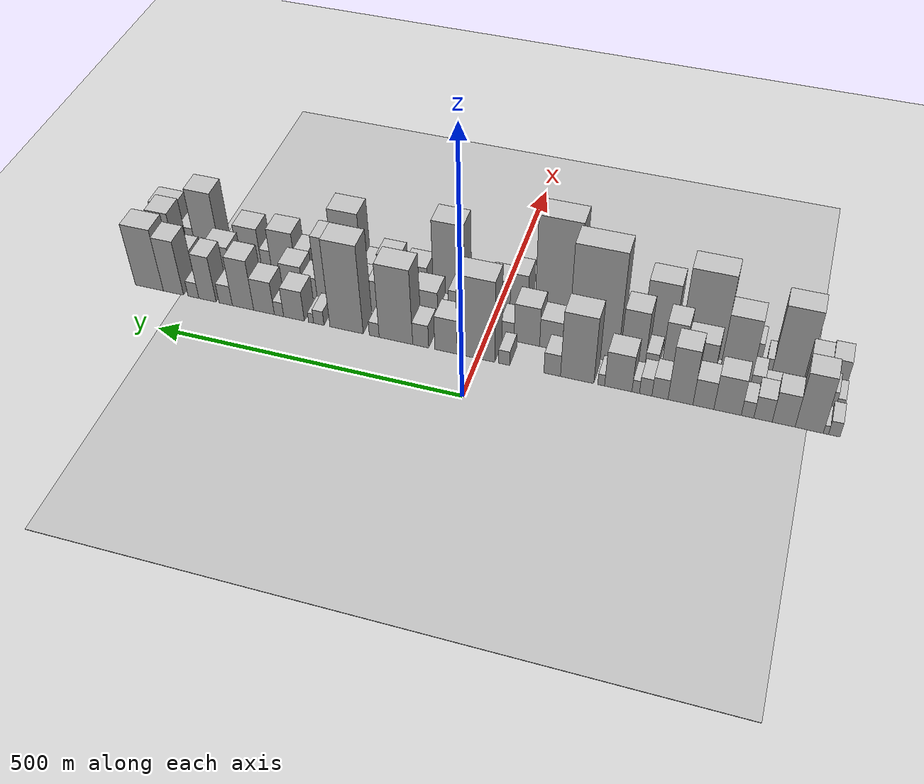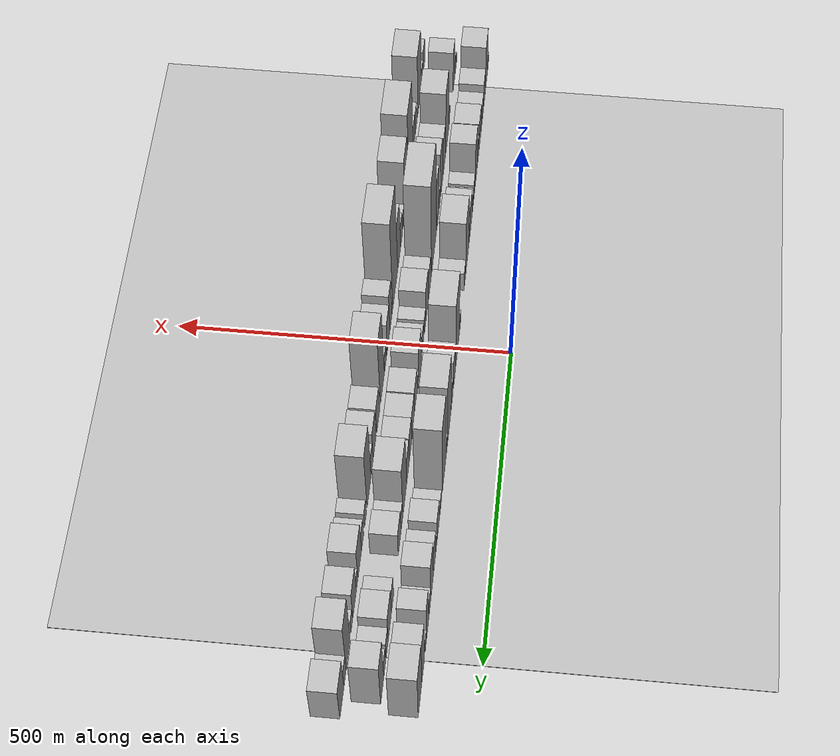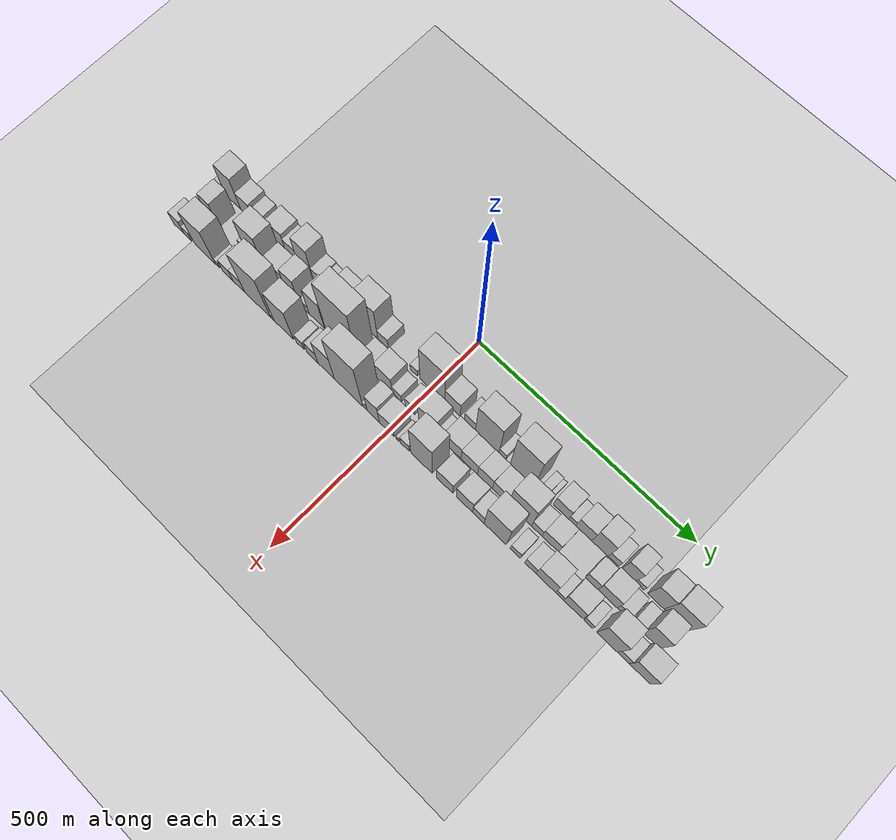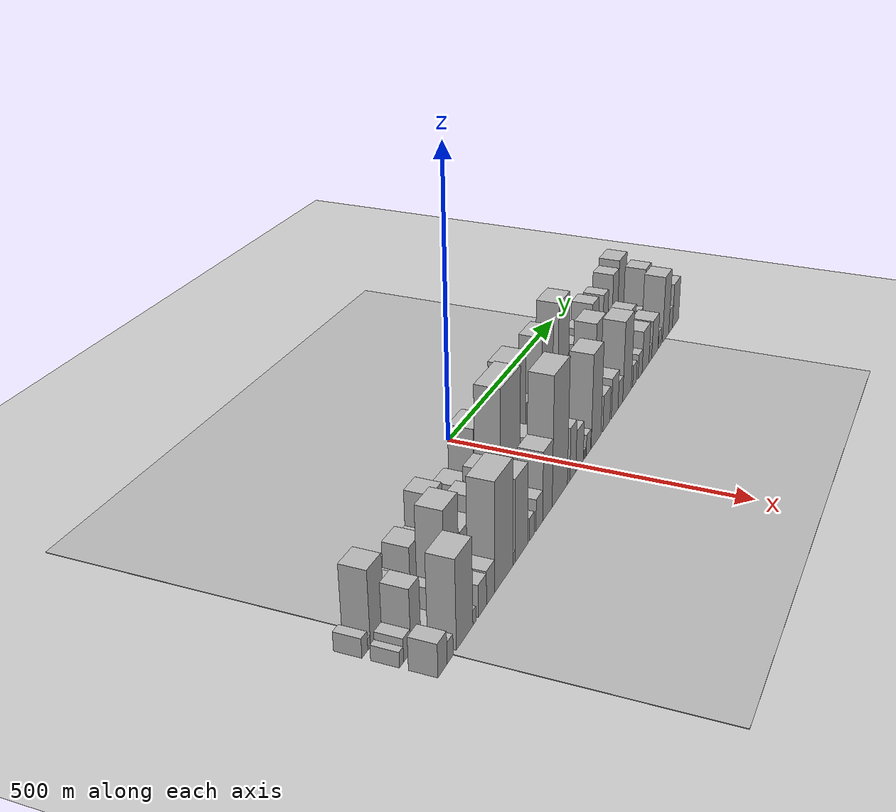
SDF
<?xml version="1.0" encoding="utf-8"?>

<sdf version="1.6">

   <world name="default">

      <gui fullscreen="0">

         <camera name="user_camera">

            <pose>-15 0 4.57585 0 0 0</pose>

            <view_controller>orbit</view_controller>

         </camera>

      </gui>

      <scene>

         <sky>

           <clouds>

             <speed>12</speed>

           </clouds>

         </sky>

         <ambient>0.4 0.4 0.4 1</ambient>

         <background>0.7 0.7 0.7 1</background>

         <shadows>1</shadows>

      </scene>

      <gravity>0 0 -9.8066</gravity>

      <magnetic_field>6e-06 2.3e-05 -4.2e-05</magnetic_field>

      <physics default="0" name="default_physics" type="ode">

         <ode>

            <solver>

               <type>quick</type>

               <iters>10</iters>

               <sor>1.0</sor>

               <use_dynamic_moi_rescaling>0</use_dynamic_moi_rescaling>

            </solver>

            <constraints>

               <cfm>0</cfm>

               <erp>0.2</erp>

               <contact_max_correcting_vel>100</contact_max_correcting_vel>

               <contact_surface_layer>0.001</contact_surface_layer>

            </constraints>

         </ode>

         <max_step_size>0.004</max_step_size>

         <real_time_factor>1</real_time_factor>

         <real_time_update_rate>250</real_time_update_rate>

      </physics>

      <light name="sun" type="directional">

         <cast_shadows>1</cast_shadows>

         <pose>0 0 10 0 0 0</pose>

         <diffuse>0.8 0.8 0.8 1</diffuse>

         <specular>0.2 0.2 0.2 1</specular>

         <attenuation>

            <range>1000</range>

            <constant>0.9</constant>

            <linear>0.01</linear>

            <quadratic>0.001</quadratic>

         </attenuation>

         <direction>-0.5 0.1 -0.9</direction>

      </light>

      <include>

         <name>ground_plane_1</name>

         <uri>model://HANNAS_ground_plane</uri>

         <pose>0 0 0  0 0 0</pose>

      </include>

      <include>

         <name>ground_plane_2</name>

         <uri>model://HANNAS_ground_plane</uri>

         <pose>100 0 0  0 0 0</pose>

      </include>

      <model name="building_1">

         <static>1</static>

         <pose frame="">100.0000 -539.7203 0 0.000000 0.000000 0.000000</pose>

         <link name="link">

            <pose frame="">0 0 15.00 0 0 0</pose>

            <collision name="collision">

               <geometry>

                  <box>

                     <size>40.0000 16.5594 30.0000</size>

                  </box>

               </geometry>

               <max_contacts>10</max_contacts>

               <surface>

                  <contact>

                     <ode/>

                  </contact>

                  <bounce/>

                  <friction>

                     <torsional>

                        <ode/>

                     </torsional>

                     <ode/>

                  </friction>

               </surface>

            </collision>

            <visual name="visual">

               <cast_shadows>0</cast_shadows>

               <geometry>

                  <box>

                     <size>40.0000 16.5594 30.0000</size>

                  </box>

               </geometry>

               <material>

                  <script>

                     <uri>model://HANNAS_wall/materials/scripts</uri>

                     <uri>model://HANNAS_wall/materials/textures</uri>

                     <name>vrc/HANNAS_wall</name>

                  </script>

               </material>

            </visual>

            <self_collide>0</self_collide>

            <enable_wind>0</enable_wind>

            <kinematic>0</kinematic>

         </link>

      </model>

      <model name="building_2">

         <static>1</static>

         <pose frame="">100.0000 -527.6907 0 0.000000 0.000000 0.000000</pose>

         <link name="link">

            <pose frame="">0 0 9.00 0 0 0</pose>

            <collision name="collision">

               <geometry>

                  <box>

                     <size>40.0000 7.4998 18.0000</size>

                  </box>

               </geometry>

               <max_contacts>10</max_contacts>

               <surface>

                  <contact>

                     <ode/>

                  </contact>

                  <bounce/>

                  <friction>

                     <torsional>

                        <ode/>

                     </torsional>

                     <ode/>

                  </friction>

               </surface>

            </collision>

            <visual name="visual">

               <cast_shadows>0</cast_shadows>

               <geometry>

                  <box>

                     <size>40.0000 7.4998 18.0000</size>

                  </box>

               </geometry>

               <material>

                  <script>

                     <uri>model://HANNAS_wall/materials/scripts</uri>

                     <uri>model://HANNAS_wall/materials/textures</uri>

                     <name>vrc/HANNAS_wall</name>

                  </script>

               </material>

            </visual>

            <self_collide>0</self_collide>

            <enable_wind>0</enable_wind>

            <kinematic>0</kinematic>

         </link>

      </model>

      <model name="building_3">

         <static>1</static>

         <pose frame="">100.0000 -503.5868 0 0.000000 0.000000 0.000000</pose>

         <link name="link">

            <pose frame="">0 0 58.50 0 0 0</pose>

            <collision name="collision">

               <geometry>

                  <box>

                     <size>40.0000 40.7081 117.0000</size>

                  </box>

               </geometry>

               <max_contacts>10</max_contacts>

               <surface>

                  <contact>

                     <ode/>

                  </contact>

                  <bounce/>

                  <friction>

                     <torsional>

                        <ode/>

                     </torsional>

                     <ode/>

                  </friction>

               </surface>

            </collision>

            <visual name="visual">

               <cast_shadows>0</cast_shadows>

               <geometry>

                  <box>

                     <size>40.0000 40.7081 117.0000</size>

                  </box>

               </geometry>

               <material>

                  <script>

                     <uri>model://HANNAS_wall/materials/scripts</uri>

                     <uri>model://HANNAS_wall/materials/textures</uri>

                     <name>vrc/HANNAS_wall</name>

                  </script>

               </material>

            </visual>

            <self_collide>0</self_collide>

            <enable_wind>0</enable_wind>

            <kinematic>0</kinematic>

         </link>

      </model>

      <model name="building_4">

         <static>1</static>

         <pose frame="">100.0000 -466.5340 0 0.000000 0.000000 0.000000</pose>

         <link name="link">

            <pose frame="">0 0 33.00 0 0 0</pose>

            <collision name="collision">

               <geometry>

                  <box>

                     <size>40.0000 33.3975 66.0000</size>

                  </box>

               </geometry>

               <max_contacts>10</max_contacts>

               <surface>

                  <contact>

                     <ode/>

                  </contact>

                  <bounce/>

                  <friction>

                     <torsional>

                        <ode/>

                     </torsional>

                     <ode/>

                  </friction>

               </surface>

            </collision>

            <visual name="visual">

               <cast_shadows>0</cast_shadows>

               <geometry>

                  <box>

                     <size>40.0000 33.3975 66.0000</size>

                  </box>

               </geometry>

               <material>

                  <script>

                     <uri>model://HANNAS_wall/materials/scripts</uri>

                     <uri>model://HANNAS_wall/materials/textures</uri>

                     <name>vrc/HANNAS_wall</name>

                  </script>

               </material>

            </visual>

            <self_collide>0</self_collide>

            <enable_wind>0</enable_wind>

            <kinematic>0</kinematic>

         </link>

      </model>

      <model name="building_5">

         <static>1</static>

         <pose frame="">100.0000 -436.3399 0 0.000000 0.000000 0.000000</pose>

         <link name="link">

            <pose frame="">0 0 24.00 0 0 0</pose>

            <collision name="collision">

               <geometry>

                  <box>

                     <size>40.0000 26.9907 48.0000</size>

                  </box>

               </geometry>

               <max_contacts>10</max_contacts>

               <surface>

                  <contact>

                     <ode/>

                  </contact>

                  <bounce/>

                  <friction>

                     <torsional>

                        <ode/>

                     </torsional>

                     <ode/>

                  </friction>

               </surface>

            </collision>

            <visual name="visual">

               <cast_shadows>0</cast_shadows>

               <geometry>

                  <box>

                     <size>40.0000 26.9907 48.0000</size>

                  </box>

               </geometry>

               <material>

                  <script>

                     <uri>model://HANNAS_wall/materials/scripts</uri>

                     <uri>model://HANNAS_wall/materials/textures</uri>

                     <name>vrc/HANNAS_wall</name>

                  </script>

               </material>

            </visual>

            <self_collide>0</self_collide>

            <enable_wind>0</enable_wind>

            <kinematic>0</kinematic>

         </link>

      </model>

      <model name="building_6">

         <static>1</static>

         <pose frame="">100.0000 -413.6722 0 0.000000 0.000000 0.000000</pose>

         <link name="link">

            <pose frame="">0 0 16.50 0 0 0</pose>

            <collision name="collision">

               <geometry>

                  <box>

                     <size>40.0000 18.3447 33.0000</size>

                  </box>

               </geometry>

               <max_contacts>10</max_contacts>

               <surface>

                  <contact>

                     <ode/>

                  </contact>

                  <bounce/>

                  <friction>

                     <torsional>

                        <ode/>

                     </torsional>

                     <ode/>

                  </friction>

               </surface>

            </collision>

            <visual name="visual">

               <cast_shadows>0</cast_shadows>

               <geometry>

                  <box>

                     <size>40.0000 18.3447 33.0000</size>

                  </box>

               </geometry>

               <material>

                  <script>

                     <uri>model://HANNAS_wall/materials/scripts</uri>

                     <uri>model://HANNAS_wall/materials/textures</uri>

                     <name>vrc/HANNAS_wall</name>

                  </script>

               </material>

            </visual>

            <self_collide>0</self_collide>

            <enable_wind>0</enable_wind>

            <kinematic>0</kinematic>

         </link>

      </model>

      <model name="building_7">

         <static>1</static>

         <pose frame="">100.0000 -384.2251 0 0.000000 0.000000 0.000000</pose>

         <link name="link">

            <pose frame="">0 0 37.50 0 0 0</pose>

            <collision name="collision">

               <geometry>

                  <box>

                     <size>40.0000 40.5494 75.0000</size>

                  </box>

               </geometry>

               <max_contacts>10</max_contacts>

               <surface>

                  <contact>

                     <ode/>

                  </contact>

                  <bounce/>

                  <friction>

                     <torsional>

                        <ode/>

                     </torsional>

                     <ode/>

                  </friction>

               </surface>

            </collision>

            <visual name="visual">

               <cast_shadows>0</cast_shadows>

               <geometry>

                  <box>

                     <size>40.0000 40.5494 75.0000</size>

                  </box>

               </geometry>

               <material>

                  <script>

                     <uri>model://HANNAS_wall/materials/scripts</uri>

                     <uri>model://HANNAS_wall/materials/textures</uri>

                     <name>vrc/HANNAS_wall</name>

                  </script>

               </material>

            </visual>

            <self_collide>0</self_collide>

            <enable_wind>0</enable_wind>

            <kinematic>0</kinematic>

         </link>

      </model>

      <model name="building_8">

         <static>1</static>

         <pose frame="">100.0000 -348.3038 0 0.000000 0.000000 0.000000</pose>

         <link name="link">

            <pose frame="">0 0 28.50 0 0 0</pose>

            <collision name="collision">

               <geometry>

                  <box>

                     <size>40.0000 31.2933 57.0000</size>

                  </box>

               </geometry>

               <max_contacts>10</max_contacts>

               <surface>

                  <contact>

                     <ode/>

                  </contact>

                  <bounce/>

                  <friction>

                     <torsional>

                        <ode/>

                     </torsional>

                     <ode/>

                  </friction>

               </surface>

            </collision>

            <visual name="visual">

               <cast_shadows>0</cast_shadows>

               <geometry>

                  <box>

                     <size>40.0000 31.2933 57.0000</size>

                  </box>

               </geometry>

               <material>

                  <script>

                     <uri>model://HANNAS_wall/materials/scripts</uri>

                     <uri>model://HANNAS_wall/materials/textures</uri>

                     <name>vrc/HANNAS_wall</name>

                  </script>

               </material>

            </visual>

            <self_collide>0</self_collide>

            <enable_wind>0</enable_wind>

            <kinematic>0</kinematic>

         </link>

      </model>

      <model name="building_9">

         <static>1</static>

         <pose frame="">100.0000 -313.9564 0 0.000000 0.000000 0.000000</pose>

         <link name="link">

            <pose frame="">0 0 57.00 0 0 0</pose>

            <collision name="collision">

               <geometry>

                  <box>

                     <size>40.0000 37.4015 114.0000</size>

                  </box>

               </geometry>

               <max_contacts>10</max_contacts>

               <surface>

                  <contact>

                     <ode/>

                  </contact>

                  <bounce/>

                  <friction>

                     <torsional>

                        <ode/>

                     </torsional>

                     <ode/>

                  </friction>

               </surface>

            </collision>

            <visual name="visual">

               <cast_shadows>0</cast_shadows>

               <geometry>

                  <box>

                     <size>40.0000 37.4015 114.0000</size>

                  </box>

               </geometry>

               <material>

                  <script>

                     <uri>model://HANNAS_wall/materials/scripts</uri>

                     <uri>model://HANNAS_wall/materials/textures</uri>

                     <name>vrc/HANNAS_wall</name>

                  </script>

               </material>

            </visual>

            <self_collide>0</self_collide>

            <enable_wind>0</enable_wind>

            <kinematic>0</kinematic>

         </link>

      </model>

      <model name="building_10">

         <static>1</static>

         <pose frame="">100.0000 -283.1105 0 0.000000 0.000000 0.000000</pose>

         <link name="link">

            <pose frame="">0 0 21.00 0 0 0</pose>

            <collision name="collision">

               <geometry>

                  <box>

                     <size>40.0000 24.2902 42.0000</size>

                  </box>

               </geometry>

               <max_contacts>10</max_contacts>

               <surface>

                  <contact>

                     <ode/>

                  </contact>

                  <bounce/>

                  <friction>

                     <torsional>

                        <ode/>

                     </torsional>

                     <ode/>

                  </friction>

               </surface>

            </collision>

            <visual name="visual">

               <cast_shadows>0</cast_shadows>

               <geometry>

                  <box>

                     <size>40.0000 24.2902 42.0000</size>

                  </box>

               </geometry>

               <material>

                  <script>

                     <uri>model://HANNAS_wall/materials/scripts</uri>

                     <uri>model://HANNAS_wall/materials/textures</uri>

                     <name>vrc/HANNAS_wall</name>

                  </script>

               </material>

            </visual>

            <self_collide>0</self_collide>

            <enable_wind>0</enable_wind>

            <kinematic>0</kinematic>

         </link>

      </model>

      <model name="building_11">

         <static>1</static>

         <pose frame="">100.0000 -261.4859 0 0.000000 0.000000 0.000000</pose>

         <link name="link">

            <pose frame="">0 0 18.00 0 0 0</pose>

            <collision name="collision">

               <geometry>

                  <box>

                     <size>40.0000 18.9591 36.0000</size>

                  </box>

               </geometry>

               <max_contacts>10</max_contacts>

               <surface>

                  <contact>

                     <ode/>

                  </contact>

                  <bounce/>

                  <friction>

                     <torsional>

                        <ode/>

                     </torsional>

                     <ode/>

                  </friction>

               </surface>

            </collision>

            <visual name="visual">

               <cast_shadows>0</cast_shadows>

               <geometry>

                  <box>

                     <size>40.0000 18.9591 36.0000</size>

                  </box>

               </geometry>

               <material>

                  <script>

                     <uri>model://HANNAS_wall/materials/scripts</uri>

                     <uri>model://HANNAS_wall/materials/textures</uri>

                     <name>vrc/HANNAS_wall</name>

                  </script>

               </material>

            </visual>

            <self_collide>0</self_collide>

            <enable_wind>0</enable_wind>

            <kinematic>0</kinematic>

         </link>

      </model>

      <model name="building_12">

         <static>1</static>

         <pose frame="">100.0000 -246.2850 0 0.000000 0.000000 0.000000</pose>

         <link name="link">

            <pose frame="">0 0 13.50 0 0 0</pose>

            <collision name="collision">

               <geometry>

                  <box>

                     <size>40.0000 11.4427 27.0000</size>

                  </box>

               </geometry>

               <max_contacts>10</max_contacts>

               <surface>

                  <contact>

                     <ode/>

                  </contact>

                  <bounce/>

                  <friction>

                     <torsional>

                        <ode/>

                     </torsional>

                     <ode/>

                  </friction>

               </surface>

            </collision>

            <visual name="visual">

               <cast_shadows>0</cast_shadows>

               <geometry>

                  <box>

                     <size>40.0000 11.4427 27.0000</size>

                  </box>

               </geometry>

               <material>

                  <script>

                     <uri>model://HANNAS_wall/materials/scripts</uri>

                     <uri>model://HANNAS_wall/materials/textures</uri>

                     <name>vrc/HANNAS_wall</name>

                  </script>

               </material>

            </visual>

            <self_collide>0</self_collide>

            <enable_wind>0</enable_wind>

            <kinematic>0</kinematic>

         </link>

      </model>

      <model name="building_13">

         <static>1</static>

         <pose frame="">100.0000 -219.5942 0 0.000000 0.000000 0.000000</pose>

         <link name="link">

            <pose frame="">0 0 37.50 0 0 0</pose>

            <collision name="collision">

               <geometry>

                  <box>

                     <size>40.0000 41.9387 75.0000</size>

                  </box>

               </geometry>

               <max_contacts>10</max_contacts>

               <surface>

                  <contact>

                     <ode/>

                  </contact>

                  <bounce/>

                  <friction>

                     <torsional>

                        <ode/>

                     </torsional>

                     <ode/>

                  </friction>

               </surface>

            </collision>

            <visual name="visual">

               <cast_shadows>0</cast_shadows>

               <geometry>

                  <box>

                     <size>40.0000 41.9387 75.0000</size>

                  </box>

               </geometry>

               <material>

                  <script>

                     <uri>model://HANNAS_wall/materials/scripts</uri>

                     <uri>model://HANNAS_wall/materials/textures</uri>

                     <name>vrc/HANNAS_wall</name>

                  </script>

               </material>

            </visual>

            <self_collide>0</self_collide>

            <enable_wind>0</enable_wind>

            <kinematic>0</kinematic>

         </link>

      </model>

      <model name="building_14">

         <static>1</static>

         <pose frame="">100.0000 -193.3613 0 0.000000 0.000000 0.000000</pose>

         <link name="link">

            <pose frame="">0 0 12.00 0 0 0</pose>

            <collision name="collision">

               <geometry>

                  <box>

                     <size>40.0000 10.5271 24.0000</size>

                  </box>

               </geometry>

               <max_contacts>10</max_contacts>

               <surface>

                  <contact>

                     <ode/>

                  </contact>

                  <bounce/>

                  <friction>

                     <torsional>

                        <ode/>

                     </torsional>

                     <ode/>

                  </friction>

               </surface>

            </collision>

            <visual name="visual">

               <cast_shadows>0</cast_shadows>

               <geometry>

                  <box>

                     <size>40.0000 10.5271 24.0000</size>

                  </box>

               </geometry>

               <material>

                  <script>

                     <uri>model://HANNAS_wall/materials/scripts</uri>

                     <uri>model://HANNAS_wall/materials/textures</uri>

                     <name>vrc/HANNAS_wall</name>

                  </script>

               </material>

            </visual>

            <self_collide>0</self_collide>

            <enable_wind>0</enable_wind>

            <kinematic>0</kinematic>

         </link>

      </model>

      <model name="building_15">

         <static>1</static>

         <pose frame="">100.0000 -156.2065 0 0.000000 0.000000 0.000000</pose>

         <link name="link">

            <pose frame="">0 0 69.00 0 0 0</pose>

            <collision name="collision">

               <geometry>

                  <box>

                     <size>40.0000 51.7826 138.0000</size>

                  </box>

               </geometry>

               <max_contacts>10</max_contacts>

               <surface>

                  <contact>

                     <ode/>

                  </contact>

                  <bounce/>

                  <friction>

                     <torsional>

                        <ode/>

                     </torsional>

                     <ode/>

                  </friction>

               </surface>

            </collision>

            <visual name="visual">

               <cast_shadows>0</cast_shadows>

               <geometry>

                  <box>

                     <size>40.0000 51.7826 138.0000</size>

                  </box>

               </geometry>

               <material>

                  <script>

                     <uri>model://HANNAS_wall/materials/scripts</uri>

                     <uri>model://HANNAS_wall/materials/textures</uri>

                     <name>vrc/HANNAS_wall</name>

                  </script>

               </material>

            </visual>

            <self_collide>0</self_collide>

            <enable_wind>0</enable_wind>

            <kinematic>0</kinematic>

         </link>

      </model>

      <model name="building_16">

         <static>1</static>

         <pose frame="">100.0000 -117.3530 0 0.000000 0.000000 0.000000</pose>

         <link name="link">

            <pose frame="">0 0 22.50 0 0 0</pose>

            <collision name="collision">

               <geometry>

                  <box>

                     <size>40.0000 25.9244 45.0000</size>

                  </box>

               </geometry>

               <max_contacts>10</max_contacts>

               <surface>

                  <contact>

                     <ode/>

                  </contact>

                  <bounce/>

                  <friction>

                     <torsional>

                        <ode/>

                     </torsional>

                     <ode/>

                  </friction>

               </surface>

            </collision>

            <visual name="visual">

               <cast_shadows>0</cast_shadows>

               <geometry>

                  <box>

                     <size>40.0000 25.9244 45.0000</size>

                  </box>

               </geometry>

               <material>

                  <script>

                     <uri>model://HANNAS_wall/materials/scripts</uri>

                     <uri>model://HANNAS_wall/materials/textures</uri>

                     <name>vrc/HANNAS_wall</name>

                  </script>

               </material>

            </visual>

            <self_collide>0</self_collide>

            <enable_wind>0</enable_wind>

            <kinematic>0</kinematic>

         </link>

      </model>

      <model name="building_17">

         <static>1</static>

         <pose frame="">100.0000 -41.7375 0 0.000000 0.000000 0.000000</pose>

         <link name="link">

            <pose frame="">0 0 15.00 0 0 0</pose>

            <collision name="collision">

               <geometry>

                  <box>

                     <size>40.0000 17.7689 30.0000</size>

                  </box>

               </geometry>

               <max_contacts>10</max_contacts>

               <surface>

                  <contact>

                     <ode/>

                  </contact>

                  <bounce/>

                  <friction>

                     <torsional>

                        <ode/>

                     </torsional>

                     <ode/>

                  </friction>

               </surface>

            </collision>

            <visual name="visual">

               <cast_shadows>0</cast_shadows>

               <geometry>

                  <box>

                     <size>40.0000 17.7689 30.0000</size>

                  </box>

               </geometry>

               <material>

                  <script>

                     <uri>model://HANNAS_wall/materials/scripts</uri>

                     <uri>model://HANNAS_wall/materials/textures</uri>

                     <name>vrc/HANNAS_wall</name>

                  </script>

               </material>

            </visual>

            <self_collide>0</self_collide>

            <enable_wind>0</enable_wind>

            <kinematic>0</kinematic>

         </link>

      </model>

      <model name="building_18">

         <static>1</static>

         <pose frame="">100.0000 3.3115 0 0.000000 0.000000 0.000000</pose>

         <link name="link">

            <pose frame="">0 0 84.00 0 0 0</pose>

            <collision name="collision">

               <geometry>

                  <box>

                     <size>40.0000 60.3289 168.0000</size>

                  </box>

               </geometry>

               <max_contacts>10</max_contacts>

               <surface>

                  <contact>

                     <ode/>

                  </contact>

                  <bounce/>

                  <friction>

                     <torsional>

                        <ode/>

                     </torsional>

                     <ode/>

                  </friction>

               </surface>

            </collision>

            <visual name="visual">

               <cast_shadows>0</cast_shadows>

               <geometry>

                  <box>

                     <size>40.0000 60.3289 168.0000</size>

                  </box>

               </geometry>

               <material>

                  <script>

                     <uri>model://HANNAS_wall/materials/scripts</uri>

                     <uri>model://HANNAS_wall/materials/textures</uri>

                     <name>vrc/HANNAS_wall</name>

                  </script>

               </material>

            </visual>

            <self_collide>0</self_collide>

            <enable_wind>0</enable_wind>

            <kinematic>0</kinematic>

         </link>

      </model>

      <model name="building_19">

         <static>1</static>

         <pose frame="">100.0000 51.5704 0 0.000000 0.000000 0.000000</pose>

         <link name="link">

            <pose frame="">0 0 36.00 0 0 0</pose>

            <collision name="collision">

               <geometry>

                  <box>

                     <size>40.0000 36.1889 72.0000</size>

                  </box>

               </geometry>

               <max_contacts>10</max_contacts>

               <surface>

                  <contact>

                     <ode/>

                  </contact>

                  <bounce/>

                  <friction>

                     <torsional>

                        <ode/>

                     </torsional>

                     <ode/>

                  </friction>

               </surface>

            </collision>

            <visual name="visual">

               <cast_shadows>0</cast_shadows>

               <geometry>

                  <box>

                     <size>40.0000 36.1889 72.0000</size>

                  </box>

               </geometry>

               <material>

                  <script>

                     <uri>model://HANNAS_wall/materials/scripts</uri>

                     <uri>model://HANNAS_wall/materials/textures</uri>

                     <name>vrc/HANNAS_wall</name>

                  </script>

               </material>

            </visual>

            <self_collide>0</self_collide>

            <enable_wind>0</enable_wind>

            <kinematic>0</kinematic>

         </link>

      </model>

      <model name="building_20">

         <static>1</static>

         <pose frame="">100.0000 92.7164 0 0.000000 0.000000 0.000000</pose>

         <link name="link">

            <pose frame="">0 0 24.00 0 0 0</pose>

            <collision name="collision">

               <geometry>

                  <box>

                     <size>40.0000 26.1032 48.0000</size>

                  </box>

               </geometry>

               <max_contacts>10</max_contacts>

               <surface>

                  <contact>

                     <ode/>

                  </contact>

                  <bounce/>

                  <friction>

                     <torsional>

                        <ode/>

                     </torsional>

                     <ode/>

                  </friction>

               </surface>

            </collision>

            <visual name="visual">

               <cast_shadows>0</cast_shadows>

               <geometry>

                  <box>

                     <size>40.0000 26.1032 48.0000</size>

                  </box>

               </geometry>

               <material>

                  <script>

                     <uri>model://HANNAS_wall/materials/scripts</uri>

                     <uri>model://HANNAS_wall/materials/textures</uri>

                     <name>vrc/HANNAS_wall</name>

                  </script>

               </material>

            </visual>

            <self_collide>0</self_collide>

            <enable_wind>0</enable_wind>

            <kinematic>0</kinematic>

         </link>

      </model>

      <model name="building_21">

         <static>1</static>

         <pose frame="">100.0000 133.3653 0 0.000000 0.000000 0.000000</pose>

         <link name="link">

            <pose frame="">0 0 78.00 0 0 0</pose>

            <collision name="collision">

               <geometry>

                  <box>

                     <size>40.0000 55.1945 156.0000</size>

                  </box>

               </geometry>

               <max_contacts>10</max_contacts>

               <surface>

                  <contact>

                     <ode/>

                  </contact>

                  <bounce/>

                  <friction>

                     <torsional>

                        <ode/>

                     </torsional>

                     <ode/>

                  </friction>

               </surface>

            </collision>

            <visual name="visual">

               <cast_shadows>0</cast_shadows>

               <geometry>

                  <box>

                     <size>40.0000 55.1945 156.0000</size>

                  </box>

               </geometry>

               <material>

                  <script>

                     <uri>model://HANNAS_wall/materials/scripts</uri>

                     <uri>model://HANNAS_wall/materials/textures</uri>

                     <name>vrc/HANNAS_wall</name>

                  </script>

               </material>

            </visual>

            <self_collide>0</self_collide>

            <enable_wind>0</enable_wind>

            <kinematic>0</kinematic>

         </link>

      </model>

      <model name="building_22">

         <static>1</static>

         <pose frame="">100.0000 169.1781 0 0.000000 0.000000 0.000000</pose>

         <link name="link">

            <pose frame="">0 0 15.00 0 0 0</pose>

            <collision name="collision">

               <geometry>

                  <box>

                     <size>40.0000 16.4310 30.0000</size>

                  </box>

               </geometry>

               <max_contacts>10</max_contacts>

               <surface>

                  <contact>

                     <ode/>

                  </contact>

                  <bounce/>

                  <friction>

                     <torsional>

                        <ode/>

                     </torsional>

                     <ode/>

                  </friction>

               </surface>

            </collision>

            <visual name="visual">

               <cast_shadows>0</cast_shadows>

               <geometry>

                  <box>

                     <size>40.0000 16.4310 30.0000</size>

                  </box>

               </geometry>

               <material>

                  <script>

                     <uri>model://HANNAS_wall/materials/scripts</uri>

                     <uri>model://HANNAS_wall/materials/textures</uri>

                     <name>vrc/HANNAS_wall</name>

                  </script>

               </material>

            </visual>

            <self_collide>0</self_collide>

            <enable_wind>0</enable_wind>

            <kinematic>0</kinematic>

         </link>

      </model>

      <model name="building_23">

         <static>1</static>

         <pose frame="">100.0000 215.2913 0 0.000000 0.000000 0.000000</pose>

         <link name="link">

            <pose frame="">0 0 91.50 0 0 0</pose>

            <collision name="collision">

               <geometry>

                  <box>

                     <size>40.0000 55.7954 183.0000</size>

                  </box>

               </geometry>

               <max_contacts>10</max_contacts>

               <surface>

                  <contact>

                     <ode/>

                  </contact>

                  <bounce/>

                  <friction>

                     <torsional>

                        <ode/>

                     </torsional>

                     <ode/>

                  </friction>

               </surface>

            </collision>

            <visual name="visual">

               <cast_shadows>0</cast_shadows>

               <geometry>

                  <box>

                     <size>40.0000 55.7954 183.0000</size>

                  </box>

               </geometry>

               <material>

                  <script>

                     <uri>model://HANNAS_wall/materials/scripts</uri>

                     <uri>model://HANNAS_wall/materials/textures</uri>

                     <name>vrc/HANNAS_wall</name>

                  </script>

               </material>

            </visual>

            <self_collide>0</self_collide>

            <enable_wind>0</enable_wind>

            <kinematic>0</kinematic>

         </link>

      </model>

      <model name="building_24">

         <static>1</static>

         <pose frame="">100.0000 261.9377 0 0.000000 0.000000 0.000000</pose>

         <link name="link">

            <pose frame="">0 0 15.00 0 0 0</pose>

            <collision name="collision">

               <geometry>

                  <box>

                     <size>40.0000 17.4974 30.0000</size>

                  </box>

               </geometry>

               <max_contacts>10</max_contacts>

               <surface>

                  <contact>

                     <ode/>

                  </contact>

                  <bounce/>

                  <friction>

                     <torsional>

                        <ode/>

                     </torsional>

                     <ode/>

                  </friction>

               </surface>

            </collision>

            <visual name="visual">

               <cast_shadows>0</cast_shadows>

               <geometry>

                  <box>

                     <size>40.0000 17.4974 30.0000</size>

                  </box>

               </geometry>

               <material>

                  <script>

                     <uri>model://HANNAS_wall/materials/scripts</uri>

                     <uri>model://HANNAS_wall/materials/textures</uri>

                     <name>vrc/HANNAS_wall</name>

                  </script>

               </material>

            </visual>

            <self_collide>0</self_collide>

            <enable_wind>0</enable_wind>

            <kinematic>0</kinematic>

         </link>

      </model>

      <model name="building_25">

         <static>1</static>

         <pose frame="">100.0000 275.0510 0 0.000000 0.000000 0.000000</pose>

         <link name="link">

            <pose frame="">0 0 10.50 0 0 0</pose>

            <collision name="collision">

               <geometry>

                  <box>

                     <size>40.0000 8.7292 21.0000</size>

                  </box>

               </geometry>

               <max_contacts>10</max_contacts>

               <surface>

                  <contact>

                     <ode/>

                  </contact>

                  <bounce/>

                  <friction>

                     <torsional>

                        <ode/>

                     </torsional>

                     <ode/>

                  </friction>

               </surface>

            </collision>

            <visual name="visual">

               <cast_shadows>0</cast_shadows>

               <geometry>

                  <box>

                     <size>40.0000 8.7292 21.0000</size>

                  </box>

               </geometry>

               <material>

                  <script>

                     <uri>model://HANNAS_wall/materials/scripts</uri>

                     <uri>model://HANNAS_wall/materials/textures</uri>

                     <name>vrc/HANNAS_wall</name>

                  </script>

               </material>

            </visual>

            <self_collide>0</self_collide>

            <enable_wind>0</enable_wind>

            <kinematic>0</kinematic>

         </link>

      </model>

      <model name="building_26">

         <static>1</static>

         <pose frame="">100.0000 304.0262 0 0.000000 0.000000 0.000000</pose>

         <link name="link">

            <pose frame="">0 0 31.50 0 0 0</pose>

            <collision name="collision">

               <geometry>

                  <box>

                     <size>40.0000 35.2212 63.0000</size>

                  </box>

               </geometry>

               <max_contacts>10</max_contacts>

               <surface>

                  <contact>

                     <ode/>

                  </contact>

                  <bounce/>

                  <friction>

                     <torsional>

                        <ode/>

                     </torsional>

                     <ode/>

                  </friction>

               </surface>

            </collision>

            <visual name="visual">

               <cast_shadows>0</cast_shadows>

               <geometry>

                  <box>

                     <size>40.0000 35.2212 63.0000</size>

                  </box>

               </geometry>

               <material>

                  <script>

                     <uri>model://HANNAS_wall/materials/scripts</uri>

                     <uri>model://HANNAS_wall/materials/textures</uri>

                     <name>vrc/HANNAS_wall</name>

                  </script>

               </material>

            </visual>

            <self_collide>0</self_collide>

            <enable_wind>0</enable_wind>

            <kinematic>0</kinematic>

         </link>

      </model>

      <model name="building_27">

         <static>1</static>

         <pose frame="">100.0000 329.5936 0 0.000000 0.000000 0.000000</pose>

         <link name="link">

            <pose frame="">0 0 15.00 0 0 0</pose>

            <collision name="collision">

               <geometry>

                  <box>

                     <size>40.0000 15.9137 30.0000</size>

                  </box>

               </geometry>

               <max_contacts>10</max_contacts>

               <surface>

                  <contact>

                     <ode/>

                  </contact>

                  <bounce/>

                  <friction>

                     <torsional>

                        <ode/>

                     </torsional>

                     <ode/>

                  </friction>

               </surface>

            </collision>

            <visual name="visual">

               <cast_shadows>0</cast_shadows>

               <geometry>

                  <box>

                     <size>40.0000 15.9137 30.0000</size>

                  </box>

               </geometry>

               <material>

                  <script>

                     <uri>model://HANNAS_wall/materials/scripts</uri>

                     <uri>model://HANNAS_wall/materials/textures</uri>

                     <name>vrc/HANNAS_wall</name>

                  </script>

               </material>

            </visual>

            <self_collide>0</self_collide>

            <enable_wind>0</enable_wind>

            <kinematic>0</kinematic>

         </link>

      </model>

      <model name="building_28">

         <static>1</static>

         <pose frame="">100.0000 355.3646 0 0.000000 0.000000 0.000000</pose>

         <link name="link">

            <pose frame="">0 0 34.50 0 0 0</pose>

            <collision name="collision">

               <geometry>

                  <box>

                     <size>40.0000 35.6282 69.0000</size>

                  </box>

               </geometry>

               <max_contacts>10</max_contacts>

               <surface>

                  <contact>

                     <ode/>

                  </contact>

                  <bounce/>

                  <friction>

                     <torsional>

                        <ode/>

                     </torsional>

                     <ode/>

                  </friction>

               </surface>

            </collision>

            <visual name="visual">

               <cast_shadows>0</cast_shadows>

               <geometry>

                  <box>

                     <size>40.0000 35.6282 69.0000</size>

                  </box>

               </geometry>

               <material>

                  <script>

                     <uri>model://HANNAS_wall/materials/scripts</uri>

                     <uri>model://HANNAS_wall/materials/textures</uri>

                     <name>vrc/HANNAS_wall</name>

                  </script>

               </material>

            </visual>

            <self_collide>0</self_collide>

            <enable_wind>0</enable_wind>

            <kinematic>0</kinematic>

         </link>

      </model>

      <model name="building_29">

         <static>1</static>

         <pose frame="">100.0000 391.6366 0 0.000000 0.000000 0.000000</pose>

         <link name="link">

            <pose frame="">0 0 52.50 0 0 0</pose>

            <collision name="collision">

               <geometry>

                  <box>

                     <size>40.0000 36.9157 105.0000</size>

                  </box>

               </geometry>

               <max_contacts>10</max_contacts>

               <surface>

                  <contact>

                     <ode/>

                  </contact>

                  <bounce/>

                  <friction>

                     <torsional>

                        <ode/>

                     </torsional>

                     <ode/>

                  </friction>

               </surface>

            </collision>

            <visual name="visual">

               <cast_shadows>0</cast_shadows>

               <geometry>

                  <box>

                     <size>40.0000 36.9157 105.0000</size>

                  </box>

               </geometry>

               <material>

                  <script>

                     <uri>model://HANNAS_wall/materials/scripts</uri>

                     <uri>model://HANNAS_wall/materials/textures</uri>

                     <name>vrc/HANNAS_wall</name>

                  </script>

               </material>

            </visual>

            <self_collide>0</self_collide>

            <enable_wind>0</enable_wind>

            <kinematic>0</kinematic>

         </link>

      </model>

      <model name="building_30">

         <static>1</static>

         <pose frame="">100.0000 421.7339 0 0.000000 0.000000 0.000000</pose>

         <link name="link">

            <pose frame="">0 0 21.00 0 0 0</pose>

            <collision name="collision">

               <geometry>

                  <box>

                     <size>40.0000 23.2790 42.0000</size>

                  </box>

               </geometry>

               <max_contacts>10</max_contacts>

               <surface>

                  <contact>

                     <ode/>

                  </contact>

                  <bounce/>

                  <friction>

                     <torsional>

                        <ode/>

                     </torsional>

                     <ode/>

                  </friction>

               </surface>

            </collision>

            <visual name="visual">

               <cast_shadows>0</cast_shadows>

               <geometry>

                  <box>

                     <size>40.0000 23.2790 42.0000</size>

                  </box>

               </geometry>

               <material>

                  <script>

                     <uri>model://HANNAS_wall/materials/scripts</uri>

                     <uri>model://HANNAS_wall/materials/textures</uri>

                     <name>vrc/HANNAS_wall</name>

                  </script>

               </material>

            </visual>

            <self_collide>0</self_collide>

            <enable_wind>0</enable_wind>

            <kinematic>0</kinematic>

         </link>

      </model>

      <model name="building_31">

         <static>1</static>

         <pose frame="">100.0000 453.5452 0 0.000000 0.000000 0.000000</pose>

         <link name="link">

            <pose frame="">0 0 48.00 0 0 0</pose>

            <collision name="collision">

               <geometry>

                  <box>

                     <size>40.0000 30.3436 96.0000</size>

                  </box>

               </geometry>

               <max_contacts>10</max_contacts>

               <surface>

                  <contact>

                     <ode/>

                  </contact>

                  <bounce/>

                  <friction>

                     <torsional>

                        <ode/>

                     </torsional>

                     <ode/>

                  </friction>

               </surface>

            </collision>

            <visual name="visual">

               <cast_shadows>0</cast_shadows>

               <geometry>

                  <box>

                     <size>40.0000 30.3436 96.0000</size>

                  </box>

               </geometry>

               <material>

                  <script>

                     <uri>model://HANNAS_wall/materials/scripts</uri>

                     <uri>model://HANNAS_wall/materials/textures</uri>

                     <name>vrc/HANNAS_wall</name>

                  </script>

               </material>

            </visual>

            <self_collide>0</self_collide>

            <enable_wind>0</enable_wind>

            <kinematic>0</kinematic>

         </link>

      </model>

      <model name="building_32">

         <static>1</static>

         <pose frame="">100.0000 478.2213 0 0.000000 0.000000 0.000000</pose>

         <link name="link">

            <pose frame="">0 0 16.50 0 0 0</pose>

            <collision name="collision">

               <geometry>

                  <box>

                     <size>40.0000 19.0085 33.0000</size>

                  </box>

               </geometry>

               <max_contacts>10</max_contacts>

               <surface>

                  <contact>

                     <ode/>

                  </contact>

                  <bounce/>

                  <friction>

                     <torsional>

                        <ode/>

                     </torsional>

                     <ode/>

                  </friction>

               </surface>

            </collision>

            <visual name="visual">

               <cast_shadows>0</cast_shadows>

               <geometry>

                  <box>

                     <size>40.0000 19.0085 33.0000</size>

                  </box>

               </geometry>

               <material>

                  <script>

                     <uri>model://HANNAS_wall/materials/scripts</uri>

                     <uri>model://HANNAS_wall/materials/textures</uri>

                     <name>vrc/HANNAS_wall</name>

                  </script>

               </material>

            </visual>

            <self_collide>0</self_collide>

            <enable_wind>0</enable_wind>

            <kinematic>0</kinematic>

         </link>

      </model>

      <model name="building_33">

         <static>1</static>

         <pose frame="">100.0000 513.7080 0 0.000000 0.000000 0.000000</pose>

         <link name="link">

            <pose frame="">0 0 57.00 0 0 0</pose>

            <collision name="collision">

               <geometry>

                  <box>

                     <size>40.0000 35.9650 114.0000</size>

                  </box>

               </geometry>

               <max_contacts>10</max_contacts>

               <surface>

                  <contact>

                     <ode/>

                  </contact>

                  <bounce/>

                  <friction>

                     <torsional>

                        <ode/>

                     </torsional>

                     <ode/>

                  </friction>

               </surface>

            </collision>

            <visual name="visual">

               <cast_shadows>0</cast_shadows>

               <geometry>

                  <box>

                     <size>40.0000 35.9650 114.0000</size>

                  </box>

               </geometry>

               <material>

                  <script>

                     <uri>model://HANNAS_wall/materials/scripts</uri>

                     <uri>model://HANNAS_wall/materials/textures</uri>

                     <name>vrc/HANNAS_wall</name>

                  </script>

               </material>

            </visual>

            <self_collide>0</self_collide>

            <enable_wind>0</enable_wind>

            <kinematic>0</kinematic>

         </link>

      </model>

      <model name="building_34">

         <static>1</static>

         <pose frame="">100.0000 556.5723 0 0.000000 0.000000 0.000000</pose>

         <link name="link">

            <pose frame="">0 0 64.50 0 0 0</pose>

            <collision name="collision">

               <geometry>

                  <box>

                     <size>40.0000 49.7636 129.0000</size>

                  </box>

               </geometry>

               <max_contacts>10</max_contacts>

               <surface>

                  <contact>

                     <ode/>

                  </contact>

                  <bounce/>

                  <friction>

                     <torsional>

                        <ode/>

                     </torsional>

                     <ode/>

                  </friction>

               </surface>

            </collision>

            <visual name="visual">

               <cast_shadows>0</cast_shadows>

               <geometry>

                  <box>

                     <size>40.0000 49.7636 129.0000</size>

                  </box>

               </geometry>

               <material>

                  <script>

                     <uri>model://HANNAS_wall/materials/scripts</uri>

                     <uri>model://HANNAS_wall/materials/textures</uri>

                     <name>vrc/HANNAS_wall</name>

                  </script>

               </material>

            </visual>

            <self_collide>0</self_collide>

            <enable_wind>0</enable_wind>

            <kinematic>0</kinematic>

         </link>

      </model>

      <model name="building_35">

         <static>1</static>

         <pose frame="">152.0000 -542.0256 0 0.000000 0.000000 0.000000</pose>

         <link name="link">

            <pose frame="">0 0 12.00 0 0 0</pose>

            <collision name="collision">

               <geometry>

                  <box>

                     <size>40.0000 11.9488 24.0000</size>

                  </box>

               </geometry>

               <max_contacts>10</max_contacts>

               <surface>

                  <contact>

                     <ode/>

                  </contact>

                  <bounce/>

                  <friction>

                     <torsional>

                        <ode/>

                     </torsional>

                     <ode/>

                  </friction>

               </surface>

            </collision>

            <visual name="visual">

               <cast_shadows>0</cast_shadows>

               <geometry>

                  <box>

                     <size>40.0000 11.9488 24.0000</size>

                  </box>

               </geometry>

               <material>

                  <script>

                     <uri>model://HANNAS_wall/materials/scripts</uri>

                     <uri>model://HANNAS_wall/materials/textures</uri>

                     <name>vrc/HANNAS_wall</name>

                  </script>

               </material>

            </visual>

            <self_collide>0</self_collide>

            <enable_wind>0</enable_wind>

            <kinematic>0</kinematic>

         </link>

      </model>

      <model name="building_36">

         <static>1</static>

         <pose frame="">152.0000 -525.3995 0 0.000000 0.000000 0.000000</pose>

         <link name="link">

            <pose frame="">0 0 18.00 0 0 0</pose>

            <collision name="collision">

               <geometry>

                  <box>

                     <size>40.0000 21.3033 36.0000</size>

                  </box>

               </geometry>

               <max_contacts>10</max_contacts>

               <surface>

                  <contact>

                     <ode/>

                  </contact>

                  <bounce/>

                  <friction>

                     <torsional>

                        <ode/>

                     </torsional>

                     <ode/>

                  </friction>

               </surface>

            </collision>

            <visual name="visual">

               <cast_shadows>0</cast_shadows>

               <geometry>

                  <box>

                     <size>40.0000 21.3033 36.0000</size>

                  </box>

               </geometry>

               <material>

                  <script>

                     <uri>model://HANNAS_wall/materials/scripts</uri>

                     <uri>model://HANNAS_wall/materials/textures</uri>

                     <name>vrc/HANNAS_wall</name>

                  </script>

               </material>

            </visual>

            <self_collide>0</self_collide>

            <enable_wind>0</enable_wind>

            <kinematic>0</kinematic>

         </link>

      </model>

      <model name="building_37">

         <static>1</static>

         <pose frame="">152.0000 -499.8184 0 0.000000 0.000000 0.000000</pose>

         <link name="link">

            <pose frame="">0 0 48.00 0 0 0</pose>

            <collision name="collision">

               <geometry>

                  <box>

                     <size>40.0000 29.8588 96.0000</size>

                  </box>

               </geometry>

               <max_contacts>10</max_contacts>

               <surface>

                  <contact>

                     <ode/>

                  </contact>

                  <bounce/>

                  <friction>

                     <torsional>

                        <ode/>

                     </torsional>

                     <ode/>

                  </friction>

               </surface>

            </collision>

            <visual name="visual">

               <cast_shadows>0</cast_shadows>

               <geometry>

                  <box>

                     <size>40.0000 29.8588 96.0000</size>

                  </box>

               </geometry>

               <material>

                  <script>

                     <uri>model://HANNAS_wall/materials/scripts</uri>

                     <uri>model://HANNAS_wall/materials/textures</uri>

                     <name>vrc/HANNAS_wall</name>

                  </script>

               </material>

            </visual>

            <self_collide>0</self_collide>

            <enable_wind>0</enable_wind>

            <kinematic>0</kinematic>

         </link>

      </model>

      <model name="building_38">

         <static>1</static>

         <pose frame="">152.0000 -418.8033 0 0.000000 0.000000 0.000000</pose>

         <link name="link">

            <pose frame="">0 0 18.00 0 0 0</pose>

            <collision name="collision">

               <geometry>

                  <box>

                     <size>40.0000 20.0571 36.0000</size>

                  </box>

               </geometry>

               <max_contacts>10</max_contacts>

               <surface>

                  <contact>

                     <ode/>

                  </contact>

                  <bounce/>

                  <friction>

                     <torsional>

                        <ode/>

                     </torsional>

                     <ode/>

                  </friction>

               </surface>

            </collision>

            <visual name="visual">

               <cast_shadows>0</cast_shadows>

               <geometry>

                  <box>

                     <size>40.0000 20.0571 36.0000</size>

                  </box>

               </geometry>

               <material>

                  <script>

                     <uri>model://HANNAS_wall/materials/scripts</uri>

                     <uri>model://HANNAS_wall/materials/textures</uri>

                     <name>vrc/HANNAS_wall</name>

                  </script>

               </material>

            </visual>

            <self_collide>0</self_collide>

            <enable_wind>0</enable_wind>

            <kinematic>0</kinematic>

         </link>

      </model>

      <model name="building_39">

         <static>1</static>

         <pose frame="">152.0000 -384.7673 0 0.000000 0.000000 0.000000</pose>

         <link name="link">

            <pose frame="">0 0 73.50 0 0 0</pose>

            <collision name="collision">

               <geometry>

                  <box>

                     <size>40.0000 48.0148 147.0000</size>

                  </box>

               </geometry>

               <max_contacts>10</max_contacts>

               <surface>

                  <contact>

                     <ode/>

                  </contact>

                  <bounce/>

                  <friction>

                     <torsional>

                        <ode/>

                     </torsional>

                     <ode/>

                  </friction>

               </surface>

            </collision>

            <visual name="visual">

               <cast_shadows>0</cast_shadows>

               <geometry>

                  <box>

                     <size>40.0000 48.0148 147.0000</size>

                  </box>

               </geometry>

               <material>

                  <script>

                     <uri>model://HANNAS_wall/materials/scripts</uri>

                     <uri>model://HANNAS_wall/materials/textures</uri>

                     <name>vrc/HANNAS_wall</name>

                  </script>

               </material>

            </visual>

            <self_collide>0</self_collide>

            <enable_wind>0</enable_wind>

            <kinematic>0</kinematic>

         </link>

      </model>

      <model name="building_40">

         <static>1</static>

         <pose frame="">152.0000 -331.0103 0 0.000000 0.000000 0.000000</pose>

         <link name="link">

            <pose frame="">0 0 40.50 0 0 0</pose>

            <collision name="collision">

               <geometry>

                  <box>

                     <size>40.0000 47.4994 81.0000</size>

                  </box>

               </geometry>

               <max_contacts>10</max_contacts>

               <surface>

                  <contact>

                     <ode/>

                  </contact>

                  <bounce/>

                  <friction>

                     <torsional>

                        <ode/>

                     </torsional>

                     <ode/>

                  </friction>

               </surface>

            </collision>

            <visual name="visual">

               <cast_shadows>0</cast_shadows>

               <geometry>

                  <box>

                     <size>40.0000 47.4994 81.0000</size>

                  </box>

               </geometry>

               <material>

                  <script>

                     <uri>model://HANNAS_wall/materials/scripts</uri>

                     <uri>model://HANNAS_wall/materials/textures</uri>

                     <name>vrc/HANNAS_wall</name>

                  </script>

               </material>

            </visual>

            <self_collide>0</self_collide>

            <enable_wind>0</enable_wind>

            <kinematic>0</kinematic>

         </link>

      </model>

      <model name="building_41">

         <static>1</static>

         <pose frame="">152.0000 -290.8518 0 0.000000 0.000000 0.000000</pose>

         <link name="link">

            <pose frame="">0 0 54.00 0 0 0</pose>

            <collision name="collision">

               <geometry>

                  <box>

                     <size>40.0000 32.8174 108.0000</size>

                  </box>

               </geometry>

               <max_contacts>10</max_contacts>

               <surface>

                  <contact>

                     <ode/>

                  </contact>

                  <bounce/>

                  <friction>

                     <torsional>

                        <ode/>

                     </torsional>

                     <ode/>

                  </friction>

               </surface>

            </collision>

            <visual name="visual">

               <cast_shadows>0</cast_shadows>

               <geometry>

                  <box>

                     <size>40.0000 32.8174 108.0000</size>

                  </box>

               </geometry>

               <material>

                  <script>

                     <uri>model://HANNAS_wall/materials/scripts</uri>

                     <uri>model://HANNAS_wall/materials/textures</uri>

                     <name>vrc/HANNAS_wall</name>

                  </script>

               </material>

            </visual>

            <self_collide>0</self_collide>

            <enable_wind>0</enable_wind>

            <kinematic>0</kinematic>

         </link>

      </model>

      <model name="building_42">

         <static>1</static>

         <pose frame="">152.0000 -259.4082 0 0.000000 0.000000 0.000000</pose>

         <link name="link">

            <pose frame="">0 0 18.00 0 0 0</pose>

            <collision name="collision">

               <geometry>

                  <box>

                     <size>40.0000 20.0698 36.0000</size>

                  </box>

               </geometry>

               <max_contacts>10</max_contacts>

               <surface>

                  <contact>

                     <ode/>

                  </contact>

                  <bounce/>

                  <friction>

                     <torsional>

                        <ode/>

                     </torsional>

                     <ode/>

                  </friction>

               </surface>

            </collision>

            <visual name="visual">

               <cast_shadows>0</cast_shadows>

               <geometry>

                  <box>

                     <size>40.0000 20.0698 36.0000</size>

                  </box>

               </geometry>

               <material>

                  <script>

                     <uri>model://HANNAS_wall/materials/scripts</uri>

                     <uri>model://HANNAS_wall/materials/textures</uri>

                     <name>vrc/HANNAS_wall</name>

                  </script>

               </material>

            </visual>

            <self_collide>0</self_collide>

            <enable_wind>0</enable_wind>

            <kinematic>0</kinematic>

         </link>

      </model>

      <model name="building_43">

         <static>1</static>

         <pose frame="">152.0000 -229.8704 0 0.000000 0.000000 0.000000</pose>

         <link name="link">

            <pose frame="">0 0 58.50 0 0 0</pose>

            <collision name="collision">

               <geometry>

                  <box>

                     <size>40.0000 39.0057 117.0000</size>

                  </box>

               </geometry>

               <max_contacts>10</max_contacts>

               <surface>

                  <contact>

                     <ode/>

                  </contact>

                  <bounce/>

                  <friction>

                     <torsional>

                        <ode/>

                     </torsional>

                     <ode/>

                  </friction>

               </surface>

            </collision>

            <visual name="visual">

               <cast_shadows>0</cast_shadows>

               <geometry>

                  <box>

                     <size>40.0000 39.0057 117.0000</size>

                  </box>

               </geometry>

               <material>

                  <script>

                     <uri>model://HANNAS_wall/materials/scripts</uri>

                     <uri>model://HANNAS_wall/materials/textures</uri>

                     <name>vrc/HANNAS_wall</name>

                  </script>

               </material>

            </visual>

            <self_collide>0</self_collide>

            <enable_wind>0</enable_wind>

            <kinematic>0</kinematic>

         </link>

      </model>

      <model name="building_44">

         <static>1</static>

         <pose frame="">152.0000 -168.1744 0 0.000000 0.000000 0.000000</pose>

         <link name="link">

            <pose frame="">0 0 112.50 0 0 0</pose>

            <collision name="collision">

               <geometry>

                  <box>

                     <size>40.0000 78.3864 225.0000</size>

                  </box>

               </geometry>

               <max_contacts>10</max_contacts>

               <surface>

                  <contact>

                     <ode/>

                  </contact>

                  <bounce/>

                  <friction>

                     <torsional>

                        <ode/>

                     </torsional>

                     <ode/>

                  </friction>

               </surface>

            </collision>

            <visual name="visual">

               <cast_shadows>0</cast_shadows>

               <geometry>

                  <box>

                     <size>40.0000 78.3864 225.0000</size>

                  </box>

               </geometry>

               <material>

                  <script>

                     <uri>model://HANNAS_wall/materials/scripts</uri>

                     <uri>model://HANNAS_wall/materials/textures</uri>

                     <name>vrc/HANNAS_wall</name>

                  </script>

               </material>

            </visual>

            <self_collide>0</self_collide>

            <enable_wind>0</enable_wind>

            <kinematic>0</kinematic>

         </link>

      </model>

      <model name="building_45">

         <static>1</static>

         <pose frame="">152.0000 -102.0199 0 0.000000 0.000000 0.000000</pose>

         <link name="link">

            <pose frame="">0 0 30.00 0 0 0</pose>

            <collision name="collision">

               <geometry>

                  <box>

                     <size>40.0000 35.9226 60.0000</size>

                  </box>

               </geometry>

               <max_contacts>10</max_contacts>

               <surface>

                  <contact>

                     <ode/>

                  </contact>

                  <bounce/>

                  <friction>

                     <torsional>

                        <ode/>

                     </torsional>

                     <ode/>

                  </friction>

               </surface>

            </collision>

            <visual name="visual">

               <cast_shadows>0</cast_shadows>

               <geometry>

                  <box>

                     <size>40.0000 35.9226 60.0000</size>

                  </box>

               </geometry>

               <material>

                  <script>

                     <uri>model://HANNAS_wall/materials/scripts</uri>

                     <uri>model://HANNAS_wall/materials/textures</uri>

                     <name>vrc/HANNAS_wall</name>

                  </script>

               </material>

            </visual>

            <self_collide>0</self_collide>

            <enable_wind>0</enable_wind>

            <kinematic>0</kinematic>

         </link>

      </model>

      <model name="building_46">

         <static>1</static>

         <pose frame="">152.0000 -63.4967 0 0.000000 0.000000 0.000000</pose>

         <link name="link">

            <pose frame="">0 0 40.50 0 0 0</pose>

            <collision name="collision">

               <geometry>

                  <box>

                     <size>40.0000 41.1237 81.0000</size>

                  </box>

               </geometry>

               <max_contacts>10</max_contacts>

               <surface>

                  <contact>

                     <ode/>

                  </contact>

                  <bounce/>

                  <friction>

                     <torsional>

                        <ode/>

                     </torsional>

                     <ode/>

                  </friction>

               </surface>

            </collision>

            <visual name="visual">

               <cast_shadows>0</cast_shadows>

               <geometry>

                  <box>

                     <size>40.0000 41.1237 81.0000</size>

                  </box>

               </geometry>

               <material>

                  <script>

                     <uri>model://HANNAS_wall/materials/scripts</uri>

                     <uri>model://HANNAS_wall/materials/textures</uri>

                     <name>vrc/HANNAS_wall</name>

                  </script>

               </material>

            </visual>

            <self_collide>0</self_collide>

            <enable_wind>0</enable_wind>

            <kinematic>0</kinematic>

         </link>

      </model>

      <model name="building_47">

         <static>1</static>

         <pose frame="">152.0000 -31.5005 0 0.000000 0.000000 0.000000</pose>

         <link name="link">

            <pose frame="">0 0 19.50 0 0 0</pose>

            <collision name="collision">

               <geometry>

                  <box>

                     <size>40.0000 22.8687 39.0000</size>

                  </box>

               </geometry>

               <max_contacts>10</max_contacts>

               <surface>

                  <contact>

                     <ode/>

                  </contact>

                  <bounce/>

                  <friction>

                     <torsional>

                        <ode/>

                     </torsional>

                     <ode/>

                  </friction>

               </surface>

            </collision>

            <visual name="visual">

               <cast_shadows>0</cast_shadows>

               <geometry>

                  <box>

                     <size>40.0000 22.8687 39.0000</size>

                  </box>

               </geometry>

               <material>

                  <script>

                     <uri>model://HANNAS_wall/materials/scripts</uri>

                     <uri>model://HANNAS_wall/materials/textures</uri>

                     <name>vrc/HANNAS_wall</name>

                  </script>

               </material>

            </visual>

            <self_collide>0</self_collide>

            <enable_wind>0</enable_wind>

            <kinematic>0</kinematic>

         </link>

      </model>

      <model name="building_48">

         <static>1</static>

         <pose frame="">152.0000 0.6745 0 0.000000 0.000000 0.000000</pose>

         <link name="link">

            <pose frame="">0 0 22.50 0 0 0</pose>

            <collision name="collision">

               <geometry>

                  <box>

                     <size>40.0000 23.4812 45.0000</size>

                  </box>

               </geometry>

               <max_contacts>10</max_contacts>

               <surface>

                  <contact>

                     <ode/>

                  </contact>

                  <bounce/>

                  <friction>

                     <torsional>

                        <ode/>

                     </torsional>

                     <ode/>

                  </friction>

               </surface>

            </collision>

            <visual name="visual">

               <cast_shadows>0</cast_shadows>

               <geometry>

                  <box>

                     <size>40.0000 23.4812 45.0000</size>

                  </box>

               </geometry>

               <material>

                  <script>

                     <uri>model://HANNAS_wall/materials/scripts</uri>

                     <uri>model://HANNAS_wall/materials/textures</uri>

                     <name>vrc/HANNAS_wall</name>

                  </script>

               </material>

            </visual>

            <self_collide>0</self_collide>

            <enable_wind>0</enable_wind>

            <kinematic>0</kinematic>

         </link>

      </model>

      <model name="building_49">

         <static>1</static>

         <pose frame="">152.0000 41.7563 0 0.000000 0.000000 0.000000</pose>

         <link name="link">

            <pose frame="">0 0 40.50 0 0 0</pose>

            <collision name="collision">

               <geometry>

                  <box>

                     <size>40.0000 42.6824 81.0000</size>

                  </box>

               </geometry>

               <max_contacts>10</max_contacts>

               <surface>

                  <contact>

                     <ode/>

                  </contact>

                  <bounce/>

                  <friction>

                     <torsional>

                        <ode/>

                     </torsional>

                     <ode/>

                  </friction>

               </surface>

            </collision>

            <visual name="visual">

               <cast_shadows>0</cast_shadows>

               <geometry>

                  <box>

                     <size>40.0000 42.6824 81.0000</size>

                  </box>

               </geometry>

               <material>

                  <script>

                     <uri>model://HANNAS_wall/materials/scripts</uri>

                     <uri>model://HANNAS_wall/materials/textures</uri>

                     <name>vrc/HANNAS_wall</name>

                  </script>

               </material>

            </visual>

            <self_collide>0</self_collide>

            <enable_wind>0</enable_wind>

            <kinematic>0</kinematic>

         </link>

      </model>

      <model name="building_50">

         <static>1</static>

         <pose frame="">152.0000 72.0934 0 0.000000 0.000000 0.000000</pose>

         <link name="link">

            <pose frame="">0 0 16.50 0 0 0</pose>

            <collision name="collision">

               <geometry>

                  <box>

                     <size>40.0000 17.9917 33.0000</size>

                  </box>

               </geometry>

               <max_contacts>10</max_contacts>

               <surface>

                  <contact>

                     <ode/>

                  </contact>

                  <bounce/>

                  <friction>

                     <torsional>

                        <ode/>

                     </torsional>

                     <ode/>

                  </friction>

               </surface>

            </collision>

            <visual name="visual">

               <cast_shadows>0</cast_shadows>

               <geometry>

                  <box>

                     <size>40.0000 17.9917 33.0000</size>

                  </box>

               </geometry>

               <material>

                  <script>

                     <uri>model://HANNAS_wall/materials/scripts</uri>

                     <uri>model://HANNAS_wall/materials/textures</uri>

                     <name>vrc/HANNAS_wall</name>

                  </script>

               </material>

            </visual>

            <self_collide>0</self_collide>

            <enable_wind>0</enable_wind>

            <kinematic>0</kinematic>

         </link>

      </model>

      <model name="building_51">

         <static>1</static>

         <pose frame="">152.0000 101.7214 0 0.000000 0.000000 0.000000</pose>

         <link name="link">

            <pose frame="">0 0 34.50 0 0 0</pose>

            <collision name="collision">

               <geometry>

                  <box>

                     <size>40.0000 41.2645 69.0000</size>

                  </box>

               </geometry>

               <max_contacts>10</max_contacts>

               <surface>

                  <contact>

                     <ode/>

                  </contact>

                  <bounce/>

                  <friction>

                     <torsional>

                        <ode/>

                     </torsional>

                     <ode/>

                  </friction>

               </surface>

            </collision>

            <visual name="visual">

               <cast_shadows>0</cast_shadows>

               <geometry>

                  <box>

                     <size>40.0000 41.2645 69.0000</size>

                  </box>

               </geometry>

               <material>

                  <script>

                     <uri>model://HANNAS_wall/materials/scripts</uri>

                     <uri>model://HANNAS_wall/materials/textures</uri>

                     <name>vrc/HANNAS_wall</name>

                  </script>

               </material>

            </visual>

            <self_collide>0</self_collide>

            <enable_wind>0</enable_wind>

            <kinematic>0</kinematic>

         </link>

      </model>

      <model name="building_52">

         <static>1</static>

         <pose frame="">152.0000 141.6499 0 0.000000 0.000000 0.000000</pose>

         <link name="link">

            <pose frame="">0 0 33.00 0 0 0</pose>

            <collision name="collision">

               <geometry>

                  <box>

                     <size>40.0000 38.5925 66.0000</size>

                  </box>

               </geometry>

               <max_contacts>10</max_contacts>

               <surface>

                  <contact>

                     <ode/>

                  </contact>

                  <bounce/>

                  <friction>

                     <torsional>

                        <ode/>

                     </torsional>

                     <ode/>

                  </friction>

               </surface>

            </collision>

            <visual name="visual">

               <cast_shadows>0</cast_shadows>

               <geometry>

                  <box>

                     <size>40.0000 38.5925 66.0000</size>

                  </box>

               </geometry>

               <material>

                  <script>

                     <uri>model://HANNAS_wall/materials/scripts</uri>

                     <uri>model://HANNAS_wall/materials/textures</uri>

                     <name>vrc/HANNAS_wall</name>

                  </script>

               </material>

            </visual>

            <self_collide>0</self_collide>

            <enable_wind>0</enable_wind>

            <kinematic>0</kinematic>

         </link>

      </model>

      <model name="building_53">

         <static>1</static>

         <pose frame="">152.0000 178.3132 0 0.000000 0.000000 0.000000</pose>

         <link name="link">

            <pose frame="">0 0 33.00 0 0 0</pose>

            <collision name="collision">

               <geometry>

                  <box>

                     <size>40.0000 34.7341 66.0000</size>

                  </box>

               </geometry>

               <max_contacts>10</max_contacts>

               <surface>

                  <contact>

                     <ode/>

                  </contact>

                  <bounce/>

                  <friction>

                     <torsional>

                        <ode/>

                     </torsional>

                     <ode/>

                  </friction>

               </surface>

            </collision>

            <visual name="visual">

               <cast_shadows>0</cast_shadows>

               <geometry>

                  <box>

                     <size>40.0000 34.7341 66.0000</size>

                  </box>

               </geometry>

               <material>

                  <script>

                     <uri>model://HANNAS_wall/materials/scripts</uri>

                     <uri>model://HANNAS_wall/materials/textures</uri>

                     <name>vrc/HANNAS_wall</name>

                  </script>

               </material>

            </visual>

            <self_collide>0</self_collide>

            <enable_wind>0</enable_wind>

            <kinematic>0</kinematic>

         </link>

      </model>

      <model name="building_54">

         <static>1</static>

         <pose frame="">152.0000 214.1476 0 0.000000 0.000000 0.000000</pose>

         <link name="link">

            <pose frame="">0 0 31.50 0 0 0</pose>

            <collision name="collision">

               <geometry>

                  <box>

                     <size>40.0000 36.9346 63.0000</size>

                  </box>

               </geometry>

               <max_contacts>10</max_contacts>

               <surface>

                  <contact>

                     <ode/>

                  </contact>

                  <bounce/>

                  <friction>

                     <torsional>

                        <ode/>

                     </torsional>

                     <ode/>

                  </friction>

               </surface>

            </collision>

            <visual name="visual">

               <cast_shadows>0</cast_shadows>

               <geometry>

                  <box>

                     <size>40.0000 36.9346 63.0000</size>

                  </box>

               </geometry>

               <material>

                  <script>

                     <uri>model://HANNAS_wall/materials/scripts</uri>

                     <uri>model://HANNAS_wall/materials/textures</uri>

                     <name>vrc/HANNAS_wall</name>

                  </script>

               </material>

            </visual>

            <self_collide>0</self_collide>

            <enable_wind>0</enable_wind>

            <kinematic>0</kinematic>

         </link>

      </model>

      <model name="building_55">

         <static>1</static>

         <pose frame="">152.0000 258.7422 0 0.000000 0.000000 0.000000</pose>

         <link name="link">

            <pose frame="">0 0 67.50 0 0 0</pose>

            <collision name="collision">

               <geometry>

                  <box>

                     <size>40.0000 52.2546 135.0000</size>

                  </box>

               </geometry>

               <max_contacts>10</max_contacts>

               <surface>

                  <contact>

                     <ode/>

                  </contact>

                  <bounce/>

                  <friction>

                     <torsional>

                        <ode/>

                     </torsional>

                     <ode/>

                  </friction>

               </surface>

            </collision>

            <visual name="visual">

               <cast_shadows>0</cast_shadows>

               <geometry>

                  <box>

                     <size>40.0000 52.2546 135.0000</size>

                  </box>

               </geometry>

               <material>

                  <script>

                     <uri>model://HANNAS_wall/materials/scripts</uri>

                     <uri>model://HANNAS_wall/materials/textures</uri>

                     <name>vrc/HANNAS_wall</name>

                  </script>

               </material>

            </visual>

            <self_collide>0</self_collide>

            <enable_wind>0</enable_wind>

            <kinematic>0</kinematic>

         </link>

      </model>

      <model name="building_56">

         <static>1</static>

         <pose frame="">152.0000 296.9692 0 0.000000 0.000000 0.000000</pose>

         <link name="link">

            <pose frame="">0 0 22.50 0 0 0</pose>

            <collision name="collision">

               <geometry>

                  <box>

                     <size>40.0000 24.1995 45.0000</size>

                  </box>

               </geometry>

               <max_contacts>10</max_contacts>

               <surface>

                  <contact>

                     <ode/>

                  </contact>

                  <bounce/>

                  <friction>

                     <torsional>

                        <ode/>

                     </torsional>

                     <ode/>

                  </friction>

               </surface>

            </collision>

            <visual name="visual">

               <cast_shadows>0</cast_shadows>

               <geometry>

                  <box>

                     <size>40.0000 24.1995 45.0000</size>

                  </box>

               </geometry>

               <material>

                  <script>

                     <uri>model://HANNAS_wall/materials/scripts</uri>

                     <uri>model://HANNAS_wall/materials/textures</uri>

                     <name>vrc/HANNAS_wall</name>

                  </script>

               </material>

            </visual>

            <self_collide>0</self_collide>

            <enable_wind>0</enable_wind>

            <kinematic>0</kinematic>

         </link>

      </model>

      <model name="building_57">

         <static>1</static>

         <pose frame="">152.0000 327.7760 0 0.000000 0.000000 0.000000</pose>

         <link name="link">

            <pose frame="">0 0 31.50 0 0 0</pose>

            <collision name="collision">

               <geometry>

                  <box>

                     <size>40.0000 37.4141 63.0000</size>

                  </box>

               </geometry>

               <max_contacts>10</max_contacts>

               <surface>

                  <contact>

                     <ode/>

                  </contact>

                  <bounce/>

                  <friction>

                     <torsional>

                        <ode/>

                     </torsional>

                     <ode/>

                  </friction>

               </surface>

            </collision>

            <visual name="visual">

               <cast_shadows>0</cast_shadows>

               <geometry>

                  <box>

                     <size>40.0000 37.4141 63.0000</size>

                  </box>

               </geometry>

               <material>

                  <script>

                     <uri>model://HANNAS_wall/materials/scripts</uri>

                     <uri>model://HANNAS_wall/materials/textures</uri>

                     <name>vrc/HANNAS_wall</name>

                  </script>

               </material>

            </visual>

            <self_collide>0</self_collide>

            <enable_wind>0</enable_wind>

            <kinematic>0</kinematic>

         </link>

      </model>

      <model name="building_58">

         <static>1</static>

         <pose frame="">152.0000 419.4962 0 0.000000 0.000000 0.000000</pose>

         <link name="link">

            <pose frame="">0 0 27.00 0 0 0</pose>

            <collision name="collision">

               <geometry>

                  <box>

                     <size>40.0000 28.0087 54.0000</size>

                  </box>

               </geometry>

               <max_contacts>10</max_contacts>

               <surface>

                  <contact>

                     <ode/>

                  </contact>

                  <bounce/>

                  <friction>

                     <torsional>

                        <ode/>

                     </torsional>

                     <ode/>

                  </friction>

               </surface>

            </collision>

            <visual name="visual">

               <cast_shadows>0</cast_shadows>

               <geometry>

                  <box>

                     <size>40.0000 28.0087 54.0000</size>

                  </box>

               </geometry>

               <material>

                  <script>

                     <uri>model://HANNAS_wall/materials/scripts</uri>

                     <uri>model://HANNAS_wall/materials/textures</uri>

                     <name>vrc/HANNAS_wall</name>

                  </script>

               </material>

            </visual>

            <self_collide>0</self_collide>

            <enable_wind>0</enable_wind>

            <kinematic>0</kinematic>

         </link>

      </model>

      <model name="building_59">

         <static>1</static>

         <pose frame="">152.0000 454.4222 0 0.000000 0.000000 0.000000</pose>

         <link name="link">

            <pose frame="">0 0 36.00 0 0 0</pose>

            <collision name="collision">

               <geometry>

                  <box>

                     <size>40.0000 41.8433 72.0000</size>

                  </box>

               </geometry>

               <max_contacts>10</max_contacts>

               <surface>

                  <contact>

                     <ode/>

                  </contact>

                  <bounce/>

                  <friction>

                     <torsional>

                        <ode/>

                     </torsional>

                     <ode/>

                  </friction>

               </surface>

            </collision>

            <visual name="visual">

               <cast_shadows>0</cast_shadows>

               <geometry>

                  <box>

                     <size>40.0000 41.8433 72.0000</size>

                  </box>

               </geometry>

               <material>

                  <script>

                     <uri>model://HANNAS_wall/materials/scripts</uri>

                     <uri>model://HANNAS_wall/materials/textures</uri>

                     <name>vrc/HANNAS_wall</name>

                  </script>

               </material>

            </visual>

            <self_collide>0</self_collide>

            <enable_wind>0</enable_wind>

            <kinematic>0</kinematic>

         </link>

      </model>

      <model name="building_60">

         <static>1</static>

         <pose frame="">152.0000 488.0636 0 0.000000 0.000000 0.000000</pose>

         <link name="link">

            <pose frame="">0 0 22.50 0 0 0</pose>

            <collision name="collision">

               <geometry>

                  <box>

                     <size>40.0000 25.4396 45.0000</size>

                  </box>

               </geometry>

               <max_contacts>10</max_contacts>

               <surface>

                  <contact>

                     <ode/>

                  </contact>

                  <bounce/>

                  <friction>

                     <torsional>

                        <ode/>

                     </torsional>

                     <ode/>

                  </friction>

               </surface>

            </collision>

            <visual name="visual">

               <cast_shadows>0</cast_shadows>

               <geometry>

                  <box>

                     <size>40.0000 25.4396 45.0000</size>

                  </box>

               </geometry>

               <material>

                  <script>

                     <uri>model://HANNAS_wall/materials/scripts</uri>

                     <uri>model://HANNAS_wall/materials/textures</uri>

                     <name>vrc/HANNAS_wall</name>

                  </script>

               </material>

            </visual>

            <self_collide>0</self_collide>

            <enable_wind>0</enable_wind>

            <kinematic>0</kinematic>

         </link>

      </model>

      <model name="building_61">

         <static>1</static>

         <pose frame="">152.0000 517.4692 0 0.000000 0.000000 0.000000</pose>

         <link name="link">

            <pose frame="">0 0 22.50 0 0 0</pose>

            <collision name="collision">

               <geometry>

                  <box>

                     <size>40.0000 23.3714 45.0000</size>

                  </box>

               </geometry>

               <max_contacts>10</max_contacts>

               <surface>

                  <contact>

                     <ode/>

                  </contact>

                  <bounce/>

                  <friction>

                     <torsional>

                        <ode/>

                     </torsional>

                     <ode/>

                  </friction>

               </surface>

            </collision>

            <visual name="visual">

               <cast_shadows>0</cast_shadows>

               <geometry>

                  <box>

                     <size>40.0000 23.3714 45.0000</size>

                  </box>

               </geometry>

               <material>

                  <script>

                     <uri>model://HANNAS_wall/materials/scripts</uri>

                     <uri>model://HANNAS_wall/materials/textures</uri>

                     <name>vrc/HANNAS_wall</name>

                  </script>

               </material>

            </visual>

            <self_collide>0</self_collide>

            <enable_wind>0</enable_wind>

            <kinematic>0</kinematic>

         </link>

      </model>

      <model name="building_62">

         <static>1</static>

         <pose frame="">152.0000 548.2094 0 0.000000 0.000000 0.000000</pose>

         <link name="link">

            <pose frame="">0 0 60.00 0 0 0</pose>

            <collision name="collision">

               <geometry>

                  <box>

                     <size>40.0000 38.1090 120.0000</size>

                  </box>

               </geometry>

               <max_contacts>10</max_contacts>

               <surface>

                  <contact>

                     <ode/>

                  </contact>

                  <bounce/>

                  <friction>

                     <torsional>

                        <ode/>

                     </torsional>

                     <ode/>

                  </friction>

               </surface>

            </collision>

            <visual name="visual">

               <cast_shadows>0</cast_shadows>

               <geometry>

                  <box>

                     <size>40.0000 38.1090 120.0000</size>

                  </box>

               </geometry>

               <material>

                  <script>

                     <uri>model://HANNAS_wall/materials/scripts</uri>

                     <uri>model://HANNAS_wall/materials/textures</uri>

                     <name>vrc/HANNAS_wall</name>

                  </script>

               </material>

            </visual>

            <self_collide>0</self_collide>

            <enable_wind>0</enable_wind>

            <kinematic>0</kinematic>

         </link>

      </model>

      <model name="building_63">

         <static>1</static>

         <pose frame="">204.0000 -533.9544 0 0.000000 0.000000 0.000000</pose>

         <link name="link">

            <pose frame="">0 0 25.50 0 0 0</pose>

            <collision name="collision">

               <geometry>

                  <box>

                     <size>40.0000 28.0912 51.0000</size>

                  </box>

               </geometry>

               <max_contacts>10</max_contacts>

               <surface>

                  <contact>

                     <ode/>

                  </contact>

                  <bounce/>

                  <friction>

                     <torsional>

                        <ode/>

                     </torsional>

                     <ode/>

                  </friction>

               </surface>

            </collision>

            <visual name="visual">

               <cast_shadows>0</cast_shadows>

               <geometry>

                  <box>

                     <size>40.0000 28.0912 51.0000</size>

                  </box>

               </geometry>

               <material>

                  <script>

                     <uri>model://HANNAS_wall/materials/scripts</uri>

                     <uri>model://HANNAS_wall/materials/textures</uri>

                     <name>vrc/HANNAS_wall</name>

                  </script>

               </material>

            </visual>

            <self_collide>0</self_collide>

            <enable_wind>0</enable_wind>

            <kinematic>0</kinematic>

         </link>

      </model>

      <model name="building_64">

         <static>1</static>

         <pose frame="">204.0000 -510.3395 0 0.000000 0.000000 0.000000</pose>

         <link name="link">

            <pose frame="">0 0 16.50 0 0 0</pose>

            <collision name="collision">

               <geometry>

                  <box>

                     <size>40.0000 19.1387 33.0000</size>

                  </box>

               </geometry>

               <max_contacts>10</max_contacts>

               <surface>

                  <contact>

                     <ode/>

                  </contact>

                  <bounce/>

                  <friction>

                     <torsional>

                        <ode/>

                     </torsional>

                     <ode/>

                  </friction>

               </surface>

            </collision>

            <visual name="visual">

               <cast_shadows>0</cast_shadows>

               <geometry>

                  <box>

                     <size>40.0000 19.1387 33.0000</size>

                  </box>

               </geometry>

               <material>

                  <script>

                     <uri>model://HANNAS_wall/materials/scripts</uri>

                     <uri>model://HANNAS_wall/materials/textures</uri>

                     <name>vrc/HANNAS_wall</name>

                  </script>

               </material>

            </visual>

            <self_collide>0</self_collide>

            <enable_wind>0</enable_wind>

            <kinematic>0</kinematic>

         </link>

      </model>

      <model name="building_65">

         <static>1</static>

         <pose frame="">204.0000 -463.7104 0 0.000000 0.000000 0.000000</pose>

         <link name="link">

            <pose frame="">0 0 69.00 0 0 0</pose>

            <collision name="collision">

               <geometry>

                  <box>

                     <size>40.0000 54.1195 138.0000</size>

                  </box>

               </geometry>

               <max_contacts>10</max_contacts>

               <surface>

                  <contact>

                     <ode/>

                  </contact>

                  <bounce/>

                  <friction>

                     <torsional>

                        <ode/>

                     </torsional>

                     <ode/>

                  </friction>

               </surface>

            </collision>

            <visual name="visual">

               <cast_shadows>0</cast_shadows>

               <geometry>

                  <box>

                     <size>40.0000 54.1195 138.0000</size>

                  </box>

               </geometry>

               <material>

                  <script>

                     <uri>model://HANNAS_wall/materials/scripts</uri>

                     <uri>model://HANNAS_wall/materials/textures</uri>

                     <name>vrc/HANNAS_wall</name>

                  </script>

               </material>

            </visual>

            <self_collide>0</self_collide>

            <enable_wind>0</enable_wind>

            <kinematic>0</kinematic>

         </link>

      </model>

      <model name="building_66">

         <static>1</static>

         <pose frame="">204.0000 -431.3526 0 0.000000 0.000000 0.000000</pose>

         <link name="link">

            <pose frame="">0 0 12.00 0 0 0</pose>

            <collision name="collision">

               <geometry>

                  <box>

                     <size>40.0000 10.5962 24.0000</size>

                  </box>

               </geometry>

               <max_contacts>10</max_contacts>

               <surface>

                  <contact>

                     <ode/>

                  </contact>

                  <bounce/>

                  <friction>

                     <torsional>

                        <ode/>

                     </torsional>

                     <ode/>

                  </friction>

               </surface>

            </collision>

            <visual name="visual">

               <cast_shadows>0</cast_shadows>

               <geometry>

                  <box>

                     <size>40.0000 10.5962 24.0000</size>

                  </box>

               </geometry>

               <material>

                  <script>

                     <uri>model://HANNAS_wall/materials/scripts</uri>

                     <uri>model://HANNAS_wall/materials/textures</uri>

                     <name>vrc/HANNAS_wall</name>

                  </script>

               </material>

            </visual>

            <self_collide>0</self_collide>

            <enable_wind>0</enable_wind>

            <kinematic>0</kinematic>

         </link>

      </model>

      <model name="building_67">

         <static>1</static>

         <pose frame="">204.0000 -403.9102 0 0.000000 0.000000 0.000000</pose>

         <link name="link">

            <pose frame="">0 0 25.50 0 0 0</pose>

            <collision name="collision">

               <geometry>

                  <box>

                     <size>40.0000 28.2884 51.0000</size>

                  </box>

               </geometry>

               <max_contacts>10</max_contacts>

               <surface>

                  <contact>

                     <ode/>

                  </contact>

                  <bounce/>

                  <friction>

                     <torsional>

                        <ode/>

                     </torsional>

                     <ode/>

                  </friction>

               </surface>

            </collision>

            <visual name="visual">

               <cast_shadows>0</cast_shadows>

               <geometry>

                  <box>

                     <size>40.0000 28.2884 51.0000</size>

                  </box>

               </geometry>

               <material>

                  <script>

                     <uri>model://HANNAS_wall/materials/scripts</uri>

                     <uri>model://HANNAS_wall/materials/textures</uri>

                     <name>vrc/HANNAS_wall</name>

                  </script>

               </material>

            </visual>

            <self_collide>0</self_collide>

            <enable_wind>0</enable_wind>

            <kinematic>0</kinematic>

         </link>

      </model>

      <model name="building_68">

         <static>1</static>

         <pose frame="">204.0000 -374.8939 0 0.000000 0.000000 0.000000</pose>

         <link name="link">

            <pose frame="">0 0 27.00 0 0 0</pose>

            <collision name="collision">

               <geometry>

                  <box>

                     <size>40.0000 29.7443 54.0000</size>

                  </box>

               </geometry>

               <max_contacts>10</max_contacts>

               <surface>

                  <contact>

                     <ode/>

                  </contact>

                  <bounce/>

                  <friction>

                     <torsional>

                        <ode/>

                     </torsional>

                     <ode/>

                  </friction>

               </surface>

            </collision>

            <visual name="visual">

               <cast_shadows>0</cast_shadows>

               <geometry>

                  <box>

                     <size>40.0000 29.7443 54.0000</size>

                  </box>

               </geometry>

               <material>

                  <script>

                     <uri>model://HANNAS_wall/materials/scripts</uri>

                     <uri>model://HANNAS_wall/materials/textures</uri>

                     <name>vrc/HANNAS_wall</name>

                  </script>

               </material>

            </visual>

            <self_collide>0</self_collide>

            <enable_wind>0</enable_wind>

            <kinematic>0</kinematic>

         </link>

      </model>

      <model name="building_69">

         <static>1</static>

         <pose frame="">204.0000 -326.7676 0 0.000000 0.000000 0.000000</pose>

         <link name="link">

            <pose frame="">0 0 87.00 0 0 0</pose>

            <collision name="collision">

               <geometry>

                  <box>

                     <size>40.0000 66.5082 174.0000</size>

                  </box>

               </geometry>

               <max_contacts>10</max_contacts>

               <surface>

                  <contact>

                     <ode/>

                  </contact>

                  <bounce/>

                  <friction>

                     <torsional>

                        <ode/>

                     </torsional>

                     <ode/>

                  </friction>

               </surface>

            </collision>

            <visual name="visual">

               <cast_shadows>0</cast_shadows>

               <geometry>

                  <box>

                     <size>40.0000 66.5082 174.0000</size>

                  </box>

               </geometry>

               <material>

                  <script>

                     <uri>model://HANNAS_wall/materials/scripts</uri>

                     <uri>model://HANNAS_wall/materials/textures</uri>

                     <name>vrc/HANNAS_wall</name>

                  </script>

               </material>

            </visual>

            <self_collide>0</self_collide>

            <enable_wind>0</enable_wind>

            <kinematic>0</kinematic>

         </link>

      </model>

      <model name="building_70">

         <static>1</static>

         <pose frame="">204.0000 -288.8050 0 0.000000 0.000000 0.000000</pose>

         <link name="link">

            <pose frame="">0 0 10.50 0 0 0</pose>

            <collision name="collision">

               <geometry>

                  <box>

                     <size>40.0000 9.4171 21.0000</size>

                  </box>

               </geometry>

               <max_contacts>10</max_contacts>

               <surface>

                  <contact>

                     <ode/>

                  </contact>

                  <bounce/>

                  <friction>

                     <torsional>

                        <ode/>

                     </torsional>

                     <ode/>

                  </friction>

               </surface>

            </collision>

            <visual name="visual">

               <cast_shadows>0</cast_shadows>

               <geometry>

                  <box>

                     <size>40.0000 9.4171 21.0000</size>

                  </box>

               </geometry>

               <material>

                  <script>

                     <uri>model://HANNAS_wall/materials/scripts</uri>

                     <uri>model://HANNAS_wall/materials/textures</uri>

                     <name>vrc/HANNAS_wall</name>

                  </script>

               </material>

            </visual>

            <self_collide>0</self_collide>

            <enable_wind>0</enable_wind>

            <kinematic>0</kinematic>

         </link>

      </model>

      <model name="building_71">

         <static>1</static>

         <pose frame="">204.0000 -259.3557 0 0.000000 0.000000 0.000000</pose>

         <link name="link">

            <pose frame="">0 0 67.50 0 0 0</pose>

            <collision name="collision">

               <geometry>

                  <box>

                     <size>40.0000 49.4816 135.0000</size>

                  </box>

               </geometry>

               <max_contacts>10</max_contacts>

               <surface>

                  <contact>

                     <ode/>

                  </contact>

                  <bounce/>

                  <friction>

                     <torsional>

                        <ode/>

                     </torsional>

                     <ode/>

                  </friction>

               </surface>

            </collision>

            <visual name="visual">

               <cast_shadows>0</cast_shadows>

               <geometry>

                  <box>

                     <size>40.0000 49.4816 135.0000</size>

                  </box>

               </geometry>

               <material>

                  <script>

                     <uri>model://HANNAS_wall/materials/scripts</uri>

                     <uri>model://HANNAS_wall/materials/textures</uri>

                     <name>vrc/HANNAS_wall</name>

                  </script>

               </material>

            </visual>

            <self_collide>0</self_collide>

            <enable_wind>0</enable_wind>

            <kinematic>0</kinematic>

         </link>

      </model>

      <model name="building_72">

         <static>1</static>

         <pose frame="">204.0000 -217.6466 0 0.000000 0.000000 0.000000</pose>

         <link name="link">

            <pose frame="">0 0 19.50 0 0 0</pose>

            <collision name="collision">

               <geometry>

                  <box>

                     <size>40.0000 19.9365 39.0000</size>

                  </box>

               </geometry>

               <max_contacts>10</max_contacts>

               <surface>

                  <contact>

                     <ode/>

                  </contact>

                  <bounce/>

                  <friction>

                     <torsional>

                        <ode/>

                     </torsional>

                     <ode/>

                  </friction>

               </surface>

            </collision>

            <visual name="visual">

               <cast_shadows>0</cast_shadows>

               <geometry>

                  <box>

                     <size>40.0000 19.9365 39.0000</size>

                  </box>

               </geometry>

               <material>

                  <script>

                     <uri>model://HANNAS_wall/materials/scripts</uri>

                     <uri>model://HANNAS_wall/materials/textures</uri>

                     <name>vrc/HANNAS_wall</name>

                  </script>

               </material>

            </visual>

            <self_collide>0</self_collide>

            <enable_wind>0</enable_wind>

            <kinematic>0</kinematic>

         </link>

      </model>

      <model name="building_73">

         <static>1</static>

         <pose frame="">204.0000 -186.7148 0 0.000000 0.000000 0.000000</pose>

         <link name="link">

            <pose frame="">0 0 27.00 0 0 0</pose>

            <collision name="collision">

               <geometry>

                  <box>

                     <size>40.0000 27.9272 54.0000</size>

                  </box>

               </geometry>

               <max_contacts>10</max_contacts>

               <surface>

                  <contact>

                     <ode/>

                  </contact>

                  <bounce/>

                  <friction>

                     <torsional>

                        <ode/>

                     </torsional>

                     <ode/>

                  </friction>

               </surface>

            </collision>

            <visual name="visual">

               <cast_shadows>0</cast_shadows>

               <geometry>

                  <box>

                     <size>40.0000 27.9272 54.0000</size>

                  </box>

               </geometry>

               <material>

                  <script>

                     <uri>model://HANNAS_wall/materials/scripts</uri>

                     <uri>model://HANNAS_wall/materials/textures</uri>

                     <name>vrc/HANNAS_wall</name>

                  </script>

               </material>

            </visual>

            <self_collide>0</self_collide>

            <enable_wind>0</enable_wind>

            <kinematic>0</kinematic>

         </link>

      </model>

      <model name="building_74">

         <static>1</static>

         <pose frame="">204.0000 -151.9746 0 0.000000 0.000000 0.000000</pose>

         <link name="link">

            <pose frame="">0 0 58.50 0 0 0</pose>

            <collision name="collision">

               <geometry>

                  <box>

                     <size>40.0000 41.5532 117.0000</size>

                  </box>

               </geometry>

               <max_contacts>10</max_contacts>

               <surface>

                  <contact>

                     <ode/>

                  </contact>

                  <bounce/>

                  <friction>

                     <torsional>

                        <ode/>

                     </torsional>

                     <ode/>

                  </friction>

               </surface>

            </collision>

            <visual name="visual">

               <cast_shadows>0</cast_shadows>

               <geometry>

                  <box>

                     <size>40.0000 41.5532 117.0000</size>

                  </box>

               </geometry>

               <material>

                  <script>

                     <uri>model://HANNAS_wall/materials/scripts</uri>

                     <uri>model://HANNAS_wall/materials/textures</uri>

                     <name>vrc/HANNAS_wall</name>

                  </script>

               </material>

            </visual>

            <self_collide>0</self_collide>

            <enable_wind>0</enable_wind>

            <kinematic>0</kinematic>

         </link>

      </model>

      <model name="building_75">

         <static>1</static>

         <pose frame="">204.0000 -96.6365 0 0.000000 0.000000 0.000000</pose>

         <link name="link">

            <pose frame="">0 0 109.50 0 0 0</pose>

            <collision name="collision">

               <geometry>

                  <box>

                     <size>40.0000 69.1231 219.0000</size>

                  </box>

               </geometry>

               <max_contacts>10</max_contacts>

               <surface>

                  <contact>

                     <ode/>

                  </contact>

                  <bounce/>

                  <friction>

                     <torsional>

                        <ode/>

                     </torsional>

                     <ode/>

                  </friction>

               </surface>

            </collision>

            <visual name="visual">

               <cast_shadows>0</cast_shadows>

               <geometry>

                  <box>

                     <size>40.0000 69.1231 219.0000</size>

                  </box>

               </geometry>

               <material>

                  <script>

                     <uri>model://HANNAS_wall/materials/scripts</uri>

                     <uri>model://HANNAS_wall/materials/textures</uri>

                     <name>vrc/HANNAS_wall</name>

                  </script>

               </material>

            </visual>

            <self_collide>0</self_collide>

            <enable_wind>0</enable_wind>

            <kinematic>0</kinematic>

         </link>

      </model>

      <model name="building_76">

         <static>1</static>

         <pose frame="">204.0000 -56.5677 0 0.000000 0.000000 0.000000</pose>

         <link name="link">

            <pose frame="">0 0 13.50 0 0 0</pose>

            <collision name="collision">

               <geometry>

                  <box>

                     <size>40.0000 11.0143 27.0000</size>

                  </box>

               </geometry>

               <max_contacts>10</max_contacts>

               <surface>

                  <contact>

                     <ode/>

                  </contact>

                  <bounce/>

                  <friction>

                     <torsional>

                        <ode/>

                     </torsional>

                     <ode/>

                  </friction>

               </surface>

            </collision>

            <visual name="visual">

               <cast_shadows>0</cast_shadows>

               <geometry>

                  <box>

                     <size>40.0000 11.0143 27.0000</size>

                  </box>

               </geometry>

               <material>

                  <script>

                     <uri>model://HANNAS_wall/materials/scripts</uri>

                     <uri>model://HANNAS_wall/materials/textures</uri>

                     <name>vrc/HANNAS_wall</name>

                  </script>

               </material>

            </visual>

            <self_collide>0</self_collide>

            <enable_wind>0</enable_wind>

            <kinematic>0</kinematic>

         </link>

      </model>

      <model name="building_77">

         <static>1</static>

         <pose frame="">204.0000 -36.4045 0 0.000000 0.000000 0.000000</pose>

         <link name="link">

            <pose frame="">0 0 46.50 0 0 0</pose>

            <collision name="collision">

               <geometry>

                  <box>

                     <size>40.0000 29.3122 93.0000</size>

                  </box>

               </geometry>

               <max_contacts>10</max_contacts>

               <surface>

                  <contact>

                     <ode/>

                  </contact>

                  <bounce/>

                  <friction>

                     <torsional>

                        <ode/>

                     </torsional>

                     <ode/>

                  </friction>

               </surface>

            </collision>

            <visual name="visual">

               <cast_shadows>0</cast_shadows>

               <geometry>

                  <box>

                     <size>40.0000 29.3122 93.0000</size>

                  </box>

               </geometry>

               <material>

                  <script>

                     <uri>model://HANNAS_wall/materials/scripts</uri>

                     <uri>model://HANNAS_wall/materials/textures</uri>

                     <name>vrc/HANNAS_wall</name>

                  </script>

               </material>

            </visual>

            <self_collide>0</self_collide>

            <enable_wind>0</enable_wind>

            <kinematic>0</kinematic>

         </link>

      </model>

      <model name="building_78">

         <static>1</static>

         <pose frame="">204.0000 -3.7217 0 0.000000 0.000000 0.000000</pose>

         <link name="link">

            <pose frame="">0 0 36.00 0 0 0</pose>

            <collision name="collision">

               <geometry>

                  <box>

                     <size>40.0000 36.0533 72.0000</size>

                  </box>

               </geometry>

               <max_contacts>10</max_contacts>

               <surface>

                  <contact>

                     <ode/>

                  </contact>

                  <bounce/>

                  <friction>

                     <torsional>

                        <ode/>

                     </torsional>

                     <ode/>

                  </friction>

               </surface>

            </collision>

            <visual name="visual">

               <cast_shadows>0</cast_shadows>

               <geometry>

                  <box>

                     <size>40.0000 36.0533 72.0000</size>

                  </box>

               </geometry>

               <material>

                  <script>

                     <uri>model://HANNAS_wall/materials/scripts</uri>

                     <uri>model://HANNAS_wall/materials/textures</uri>

                     <name>vrc/HANNAS_wall</name>

                  </script>

               </material>

            </visual>

            <self_collide>0</self_collide>

            <enable_wind>0</enable_wind>

            <kinematic>0</kinematic>

         </link>

      </model>

      <model name="building_79">

         <static>1</static>

         <pose frame="">204.0000 22.2467 0 0.000000 0.000000 0.000000</pose>

         <link name="link">

            <pose frame="">0 0 9.00 0 0 0</pose>

            <collision name="collision">

               <geometry>

                  <box>

                     <size>40.0000 7.8836 18.0000</size>

                  </box>

               </geometry>

               <max_contacts>10</max_contacts>

               <surface>

                  <contact>

                     <ode/>

                  </contact>

                  <bounce/>

                  <friction>

                     <torsional>

                        <ode/>

                     </torsional>

                     <ode/>

                  </friction>

               </surface>

            </collision>

            <visual name="visual">

               <cast_shadows>0</cast_shadows>

               <geometry>

                  <box>

                     <size>40.0000 7.8836 18.0000</size>

                  </box>

               </geometry>

               <material>

                  <script>

                     <uri>model://HANNAS_wall/materials/scripts</uri>

                     <uri>model://HANNAS_wall/materials/textures</uri>

                     <name>vrc/HANNAS_wall</name>

                  </script>

               </material>

            </visual>

            <self_collide>0</self_collide>

            <enable_wind>0</enable_wind>

            <kinematic>0</kinematic>

         </link>

      </model>

      <model name="building_80">

         <static>1</static>

         <pose frame="">204.0000 40.1122 0 0.000000 0.000000 0.000000</pose>

         <link name="link">

            <pose frame="">0 0 19.50 0 0 0</pose>

            <collision name="collision">

               <geometry>

                  <box>

                     <size>40.0000 21.8474 39.0000</size>

                  </box>

               </geometry>

               <max_contacts>10</max_contacts>

               <surface>

                  <contact>

                     <ode/>

                  </contact>

                  <bounce/>

                  <friction>

                     <torsional>

                        <ode/>

                     </torsional>

                     <ode/>

                  </friction>

               </surface>

            </collision>

            <visual name="visual">

               <cast_shadows>0</cast_shadows>

               <geometry>

                  <box>

                     <size>40.0000 21.8474 39.0000</size>

                  </box>

               </geometry>

               <material>

                  <script>

                     <uri>model://HANNAS_wall/materials/scripts</uri>

                     <uri>model://HANNAS_wall/materials/textures</uri>

                     <name>vrc/HANNAS_wall</name>

                  </script>

               </material>

            </visual>

            <self_collide>0</self_collide>

            <enable_wind>0</enable_wind>

            <kinematic>0</kinematic>

         </link>

      </model>

      <model name="building_81">

         <static>1</static>

         <pose frame="">204.0000 79.6915 0 0.000000 0.000000 0.000000</pose>

         <link name="link">

            <pose frame="">0 0 84.00 0 0 0</pose>

            <collision name="collision">

               <geometry>

                  <box>

                     <size>40.0000 51.3113 168.0000</size>

                  </box>

               </geometry>

               <max_contacts>10</max_contacts>

               <surface>

                  <contact>

                     <ode/>

                  </contact>

                  <bounce/>

                  <friction>

                     <torsional>

                        <ode/>

                     </torsional>

                     <ode/>

                  </friction>

               </surface>

            </collision>

            <visual name="visual">

               <cast_shadows>0</cast_shadows>

               <geometry>

                  <box>

                     <size>40.0000 51.3113 168.0000</size>

                  </box>

               </geometry>

               <material>

                  <script>

                     <uri>model://HANNAS_wall/materials/scripts</uri>

                     <uri>model://HANNAS_wall/materials/textures</uri>

                     <name>vrc/HANNAS_wall</name>

                  </script>

               </material>

            </visual>

            <self_collide>0</self_collide>

            <enable_wind>0</enable_wind>

            <kinematic>0</kinematic>

         </link>

      </model>

      <model name="building_82">

         <static>1</static>

         <pose frame="">204.0000 134.2931 0 0.000000 0.000000 0.000000</pose>

         <link name="link">

            <pose frame="">0 0 33.00 0 0 0</pose>

            <collision name="collision">

               <geometry>

                  <box>

                     <size>40.0000 37.8919 66.0000</size>

                  </box>

               </geometry>

               <max_contacts>10</max_contacts>

               <surface>

                  <contact>

                     <ode/>

                  </contact>

                  <bounce/>

                  <friction>

                     <torsional>

                        <ode/>

                     </torsional>

                     <ode/>

                  </friction>

               </surface>

            </collision>

            <visual name="visual">

               <cast_shadows>0</cast_shadows>

               <geometry>

                  <box>

                     <size>40.0000 37.8919 66.0000</size>

                  </box>

               </geometry>

               <material>

                  <script>

                     <uri>model://HANNAS_wall/materials/scripts</uri>

                     <uri>model://HANNAS_wall/materials/textures</uri>

                     <name>vrc/HANNAS_wall</name>

                  </script>

               </material>

            </visual>

            <self_collide>0</self_collide>

            <enable_wind>0</enable_wind>

            <kinematic>0</kinematic>

         </link>

      </model>

      <model name="building_83">

         <static>1</static>

         <pose frame="">204.0000 180.1145 0 0.000000 0.000000 0.000000</pose>

         <link name="link">

            <pose frame="">0 0 37.50 0 0 0</pose>

            <collision name="collision">

               <geometry>

                  <box>

                     <size>40.0000 37.7509 75.0000</size>

                  </box>

               </geometry>

               <max_contacts>10</max_contacts>

               <surface>

                  <contact>

                     <ode/>

                  </contact>

                  <bounce/>

                  <friction>

                     <torsional>

                        <ode/>

                     </torsional>

                     <ode/>

                  </friction>

               </surface>

            </collision>

            <visual name="visual">

               <cast_shadows>0</cast_shadows>

               <geometry>

                  <box>

                     <size>40.0000 37.7509 75.0000</size>

                  </box>

               </geometry>

               <material>

                  <script>

                     <uri>model://HANNAS_wall/materials/scripts</uri>

                     <uri>model://HANNAS_wall/materials/textures</uri>

                     <name>vrc/HANNAS_wall</name>

                  </script>

               </material>

            </visual>

            <self_collide>0</self_collide>

            <enable_wind>0</enable_wind>

            <kinematic>0</kinematic>

         </link>

      </model>

      <model name="building_84">

         <static>1</static>

         <pose frame="">204.0000 212.4514 0 0.000000 0.000000 0.000000</pose>

         <link name="link">

            <pose frame="">0 0 25.50 0 0 0</pose>

            <collision name="collision">

               <geometry>

                  <box>

                     <size>40.0000 26.9230 51.0000</size>

                  </box>

               </geometry>

               <max_contacts>10</max_contacts>

               <surface>

                  <contact>

                     <ode/>

                  </contact>

                  <bounce/>

                  <friction>

                     <torsional>

                        <ode/>

                     </torsional>

                     <ode/>

                  </friction>

               </surface>

            </collision>

            <visual name="visual">

               <cast_shadows>0</cast_shadows>

               <geometry>

                  <box>

                     <size>40.0000 26.9230 51.0000</size>

                  </box>

               </geometry>

               <material>

                  <script>

                     <uri>model://HANNAS_wall/materials/scripts</uri>

                     <uri>model://HANNAS_wall/materials/textures</uri>

                     <name>vrc/HANNAS_wall</name>

                  </script>

               </material>

            </visual>

            <self_collide>0</self_collide>

            <enable_wind>0</enable_wind>

            <kinematic>0</kinematic>

         </link>

      </model>

      <model name="building_85">

         <static>1</static>

         <pose frame="">204.0000 251.0109 0 0.000000 0.000000 0.000000</pose>

         <link name="link">

            <pose frame="">0 0 75.00 0 0 0</pose>

            <collision name="collision">

               <geometry>

                  <box>

                     <size>40.0000 50.1960 150.0000</size>

                  </box>

               </geometry>

               <max_contacts>10</max_contacts>

               <surface>

                  <contact>

                     <ode/>

                  </contact>

                  <bounce/>

                  <friction>

                     <torsional>

                        <ode/>

                     </torsional>

                     <ode/>

                  </friction>

               </surface>

            </collision>

            <visual name="visual">

               <cast_shadows>0</cast_shadows>

               <geometry>

                  <box>

                     <size>40.0000 50.1960 150.0000</size>

                  </box>

               </geometry>

               <material>

                  <script>

                     <uri>model://HANNAS_wall/materials/scripts</uri>

                     <uri>model://HANNAS_wall/materials/textures</uri>

                     <name>vrc/HANNAS_wall</name>

                  </script>

               </material>

            </visual>

            <self_collide>0</self_collide>

            <enable_wind>0</enable_wind>

            <kinematic>0</kinematic>

         </link>

      </model>

      <model name="building_86">

         <static>1</static>

         <pose frame="">204.0000 296.6893 0 0.000000 0.000000 0.000000</pose>

         <link name="link">

            <pose frame="">0 0 21.00 0 0 0</pose>

            <collision name="collision">

               <geometry>

                  <box>

                     <size>40.0000 23.1609 42.0000</size>

                  </box>

               </geometry>

               <max_contacts>10</max_contacts>

               <surface>

                  <contact>

                     <ode/>

                  </contact>

                  <bounce/>

                  <friction>

                     <torsional>

                        <ode/>

                     </torsional>

                     <ode/>

                  </friction>

               </surface>

            </collision>

            <visual name="visual">

               <cast_shadows>0</cast_shadows>

               <geometry>

                  <box>

                     <size>40.0000 23.1609 42.0000</size>

                  </box>

               </geometry>

               <material>

                  <script>

                     <uri>model://HANNAS_wall/materials/scripts</uri>

                     <uri>model://HANNAS_wall/materials/textures</uri>

                     <name>vrc/HANNAS_wall</name>

                  </script>

               </material>

            </visual>

            <self_collide>0</self_collide>

            <enable_wind>0</enable_wind>

            <kinematic>0</kinematic>

         </link>

      </model>

      <model name="building_87">

         <static>1</static>

         <pose frame="">204.0000 330.9870 0 0.000000 0.000000 0.000000</pose>

         <link name="link">

            <pose frame="">0 0 24.00 0 0 0</pose>

            <collision name="collision">

               <geometry>

                  <box>

                     <size>40.0000 25.4345 48.0000</size>

                  </box>

               </geometry>

               <max_contacts>10</max_contacts>

               <surface>

                  <contact>

                     <ode/>

                  </contact>

                  <bounce/>

                  <friction>

                     <torsional>

                        <ode/>

                     </torsional>

                     <ode/>

                  </friction>

               </surface>

            </collision>

            <visual name="visual">

               <cast_shadows>0</cast_shadows>

               <geometry>

                  <box>

                     <size>40.0000 25.4345 48.0000</size>

                  </box>

               </geometry>

               <material>

                  <script>

                     <uri>model://HANNAS_wall/materials/scripts</uri>

                     <uri>model://HANNAS_wall/materials/textures</uri>

                     <name>vrc/HANNAS_wall</name>

                  </script>

               </material>

            </visual>

            <self_collide>0</self_collide>

            <enable_wind>0</enable_wind>

            <kinematic>0</kinematic>

         </link>

      </model>

      <model name="building_88">

         <static>1</static>

         <pose frame="">204.0000 365.5047 0 0.000000 0.000000 0.000000</pose>

         <link name="link">

            <pose frame="">0 0 40.50 0 0 0</pose>

            <collision name="collision">

               <geometry>

                  <box>

                     <size>40.0000 43.6008 81.0000</size>

                  </box>

               </geometry>

               <max_contacts>10</max_contacts>

               <surface>

                  <contact>

                     <ode/>

                  </contact>

                  <bounce/>

                  <friction>

                     <torsional>

                        <ode/>

                     </torsional>

                     <ode/>

                  </friction>

               </surface>

            </collision>

            <visual name="visual">

               <cast_shadows>0</cast_shadows>

               <geometry>

                  <box>

                     <size>40.0000 43.6008 81.0000</size>

                  </box>

               </geometry>

               <material>

                  <script>

                     <uri>model://HANNAS_wall/materials/scripts</uri>

                     <uri>model://HANNAS_wall/materials/textures</uri>

                     <name>vrc/HANNAS_wall</name>

                  </script>

               </material>

            </visual>

            <self_collide>0</self_collide>

            <enable_wind>0</enable_wind>

            <kinematic>0</kinematic>

         </link>

      </model>

      <model name="building_89">

         <static>1</static>

         <pose frame="">204.0000 396.2415 0 0.000000 0.000000 0.000000</pose>

         <link name="link">

            <pose frame="">0 0 16.50 0 0 0</pose>

            <collision name="collision">

               <geometry>

                  <box>

                     <size>40.0000 17.8728 33.0000</size>

                  </box>

               </geometry>

               <max_contacts>10</max_contacts>

               <surface>

                  <contact>

                     <ode/>

                  </contact>

                  <bounce/>

                  <friction>

                     <torsional>

                        <ode/>

                     </torsional>

                     <ode/>

                  </friction>

               </surface>

            </collision>

            <visual name="visual">

               <cast_shadows>0</cast_shadows>

               <geometry>

                  <box>

                     <size>40.0000 17.8728 33.0000</size>

                  </box>

               </geometry>

               <material>

                  <script>

                     <uri>model://HANNAS_wall/materials/scripts</uri>

                     <uri>model://HANNAS_wall/materials/textures</uri>

                     <name>vrc/HANNAS_wall</name>

                  </script>

               </material>

            </visual>

            <self_collide>0</self_collide>

            <enable_wind>0</enable_wind>

            <kinematic>0</kinematic>

         </link>

      </model>

      <model name="building_90">

         <static>1</static>

         <pose frame="">204.0000 425.8992 0 0.000000 0.000000 0.000000</pose>

         <link name="link">

            <pose frame="">0 0 37.50 0 0 0</pose>

            <collision name="collision">

               <geometry>

                  <box>

                     <size>40.0000 41.4427 75.0000</size>

                  </box>

               </geometry>

               <max_contacts>10</max_contacts>

               <surface>

                  <contact>

                     <ode/>

                  </contact>

                  <bounce/>

                  <friction>

                     <torsional>

                        <ode/>

                     </torsional>

                     <ode/>

                  </friction>

               </surface>

            </collision>

            <visual name="visual">

               <cast_shadows>0</cast_shadows>

               <geometry>

                  <box>

                     <size>40.0000 41.4427 75.0000</size>

                  </box>

               </geometry>

               <material>

                  <script>

                     <uri>model://HANNAS_wall/materials/scripts</uri>

                     <uri>model://HANNAS_wall/materials/textures</uri>

                     <name>vrc/HANNAS_wall</name>

                  </script>

               </material>

            </visual>

            <self_collide>0</self_collide>

            <enable_wind>0</enable_wind>

            <kinematic>0</kinematic>

         </link>

      </model>

      <model name="building_91">

         <static>1</static>

         <pose frame="">204.0000 459.2046 0 0.000000 0.000000 0.000000</pose>

         <link name="link">

            <pose frame="">0 0 18.00 0 0 0</pose>

            <collision name="collision">

               <geometry>

                  <box>

                     <size>40.0000 19.1681 36.0000</size>

                  </box>

               </geometry>

               <max_contacts>10</max_contacts>

               <surface>

                  <contact>

                     <ode/>

                  </contact>

                  <bounce/>

                  <friction>

                     <torsional>

                        <ode/>

                     </torsional>

                     <ode/>

                  </friction>

               </surface>

            </collision>

            <visual name="visual">

               <cast_shadows>0</cast_shadows>

               <geometry>

                  <box>

                     <size>40.0000 19.1681 36.0000</size>

                  </box>

               </geometry>

               <material>

                  <script>

                     <uri>model://HANNAS_wall/materials/scripts</uri>

                     <uri>model://HANNAS_wall/materials/textures</uri>

                     <name>vrc/HANNAS_wall</name>

                  </script>

               </material>

            </visual>

            <self_collide>0</self_collide>

            <enable_wind>0</enable_wind>

            <kinematic>0</kinematic>

         </link>

      </model>

      <model name="building_92">

         <static>1</static>

         <pose frame="">204.0000 500.1604 0 0.000000 0.000000 0.000000</pose>

         <link name="link">

            <pose frame="">0 0 66.00 0 0 0</pose>

            <collision name="collision">

               <geometry>

                  <box>

                     <size>40.0000 44.7435 132.0000</size>

                  </box>

               </geometry>

               <max_contacts>10</max_contacts>

               <surface>

                  <contact>

                     <ode/>

                  </contact>

                  <bounce/>

                  <friction>

                     <torsional>

                        <ode/>

                     </torsional>

                     <ode/>

                  </friction>

               </surface>

            </collision>

            <visual name="visual">

               <cast_shadows>0</cast_shadows>

               <geometry>

                  <box>

                     <size>40.0000 44.7435 132.0000</size>

                  </box>

               </geometry>

               <material>

                  <script>

                     <uri>model://HANNAS_wall/materials/scripts</uri>

                     <uri>model://HANNAS_wall/materials/textures</uri>

                     <name>vrc/HANNAS_wall</name>

                  </script>

               </material>

            </visual>

            <self_collide>0</self_collide>

            <enable_wind>0</enable_wind>

            <kinematic>0</kinematic>

         </link>

      </model>

      <model name="building_93">

         <static>1</static>

         <pose frame="">204.0000 535.1479 0 0.000000 0.000000 0.000000</pose>

         <link name="link">

            <pose frame="">0 0 24.00 0 0 0</pose>

            <collision name="collision">

               <geometry>

                  <box>

                     <size>40.0000 25.2316 48.0000</size>

                  </box>

               </geometry>

               <max_contacts>10</max_contacts>

               <surface>

                  <contact>

                     <ode/>

                  </contact>

                  <bounce/>

                  <friction>

                     <torsional>

                        <ode/>

                     </torsional>

                     <ode/>

                  </friction>

               </surface>

            </collision>

            <visual name="visual">

               <cast_shadows>0</cast_shadows>

               <geometry>

                  <box>

                     <size>40.0000 25.2316 48.0000</size>

                  </box>

               </geometry>

               <material>

                  <script>

                     <uri>model://HANNAS_wall/materials/scripts</uri>

                     <uri>model://HANNAS_wall/materials/textures</uri>

                     <name>vrc/HANNAS_wall</name>

                  </script>

               </material>

            </visual>

            <self_collide>0</self_collide>

            <enable_wind>0</enable_wind>

            <kinematic>0</kinematic>

         </link>

      </model>

      <model name="building_94">

         <static>1</static>

         <pose frame="">204.0000 570.4630 0 0.000000 0.000000 0.000000</pose>

         <link name="link">

            <pose frame="">0 0 45.00 0 0 0</pose>

            <collision name="collision">

               <geometry>

                  <box>

                     <size>40.0000 45.3985 90.0000</size>

                  </box>

               </geometry>

               <max_contacts>10</max_contacts>

               <surface>

                  <contact>

                     <ode/>

                  </contact>

                  <bounce/>

                  <friction>

                     <torsional>

                        <ode/>

                     </torsional>

                     <ode/>

                  </friction>

               </surface>

            </collision>

            <visual name="visual">

               <cast_shadows>0</cast_shadows>

               <geometry>

                  <box>

                     <size>40.0000 45.3985 90.0000</size>

                  </box>

               </geometry>

               <material>

                  <script>

                     <uri>model://HANNAS_wall/materials/scripts</uri>

                     <uri>model://HANNAS_wall/materials/textures</uri>

                     <name>vrc/HANNAS_wall</name>

                  </script>

               </material>

            </visual>

            <self_collide>0</self_collide>

            <enable_wind>0</enable_wind>

            <kinematic>0</kinematic>

         </link>

      </model>

   </world>

</sdf>

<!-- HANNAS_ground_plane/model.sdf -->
<sdf version="1.4">
<model name="HANNAS_ground_plane">
  <static>true</static>
    <link name="link">
      <collision name="collision">
        <geometry>
          <plane>
            <normal>0 0 1</normal>
            <size>1000 1000</size>
          </plane>
        </geometry>
        <surface>
          <friction>
            <ode>
              <mu>100</mu>
              <mu2>50</mu2>
            </ode>
          </friction>
        </surface>
      </collision>
      <visual name="visual">
        <cast_shadows>false</cast_shadows>
        <geometry>
          <plane>
            <normal>0 0 1</normal>
            <size>1000 1000</size>
          </plane>
        </geometry>
        <material>
          <script>
            <uri>model://HANNAS_ground_plane/materials/scripts/HANNAS_ground_plane.material</uri>
	    <uri>model://HANNAS_ground_plane/materials/textures</uri>
            <name>HANNASGroundPlane/Image</name>
          </script>
        </material>
      </visual>
    </link>
  </model>
</sdf>
